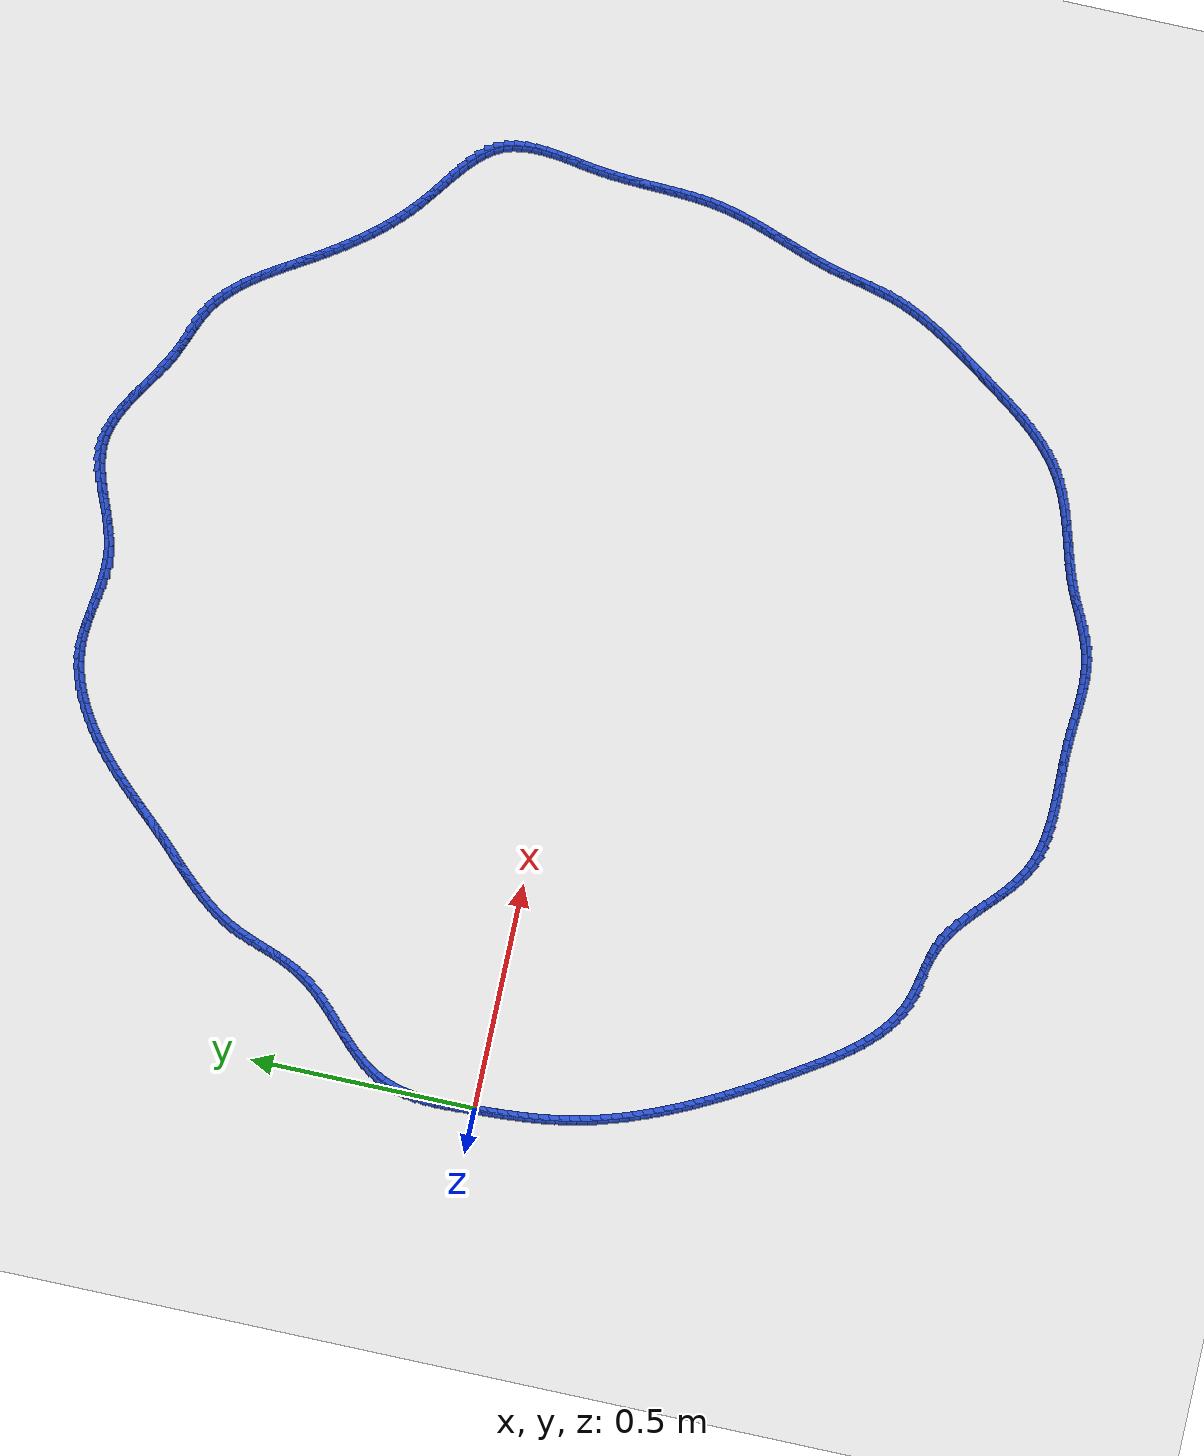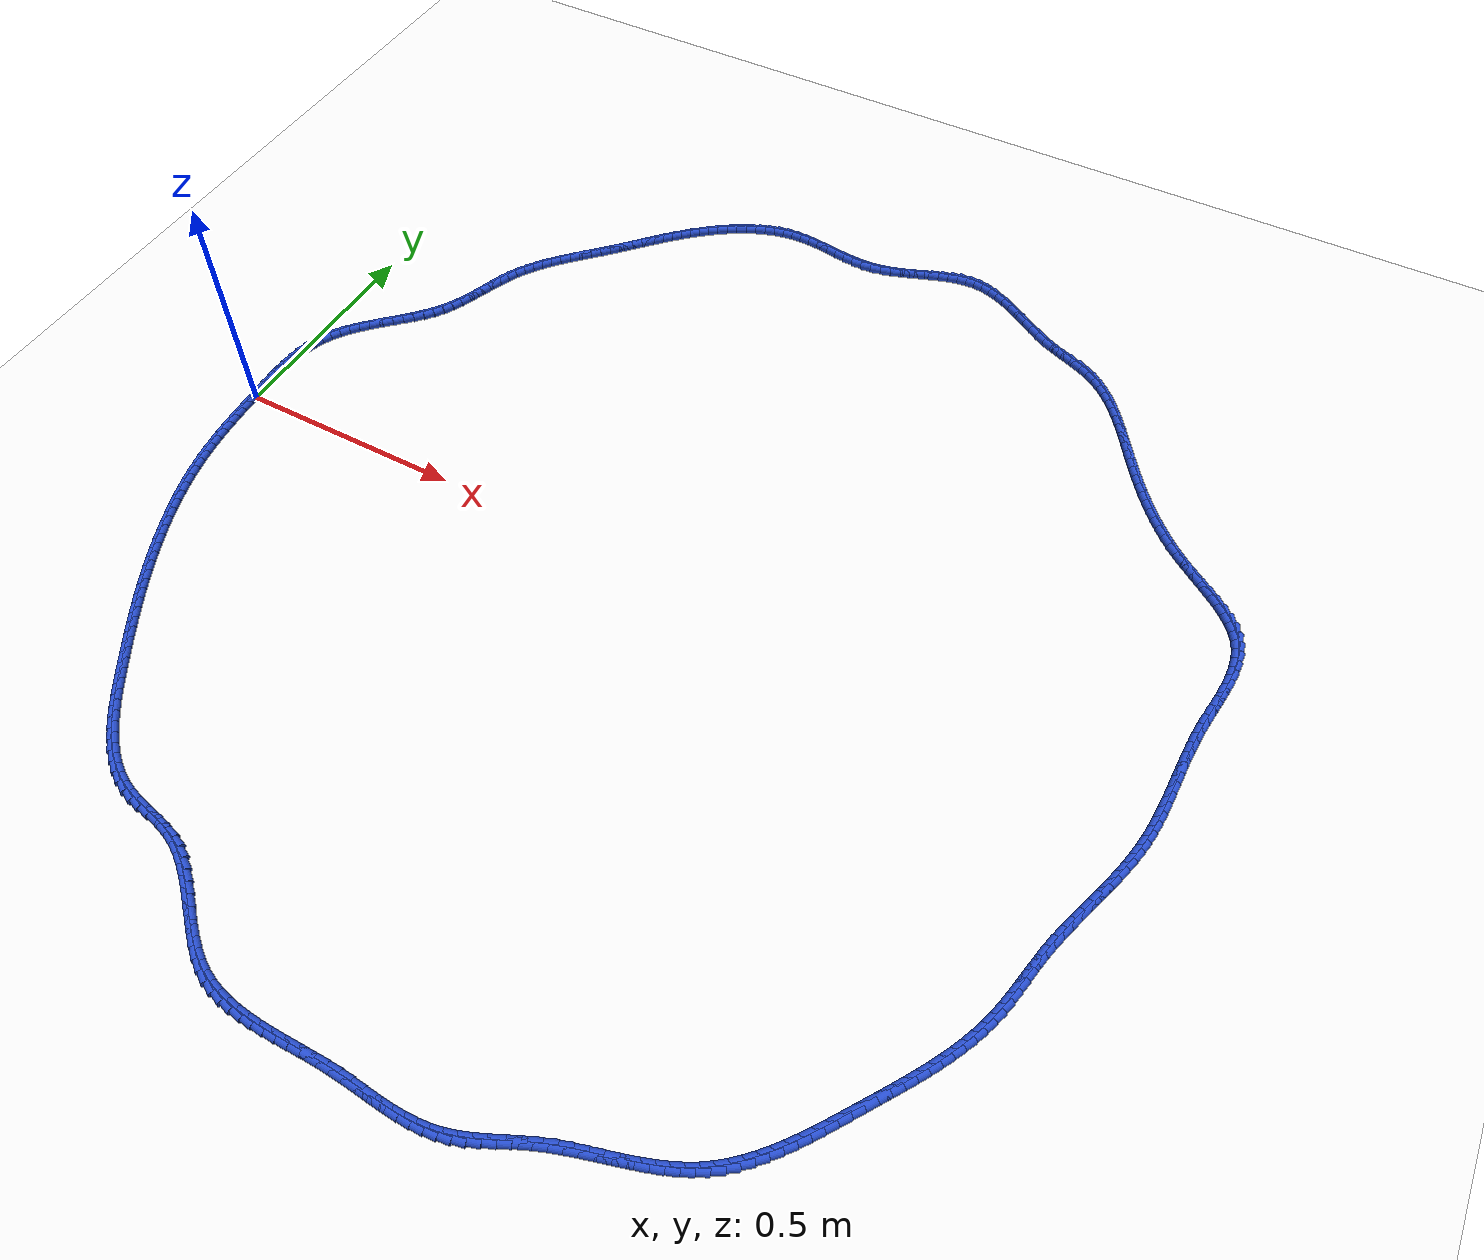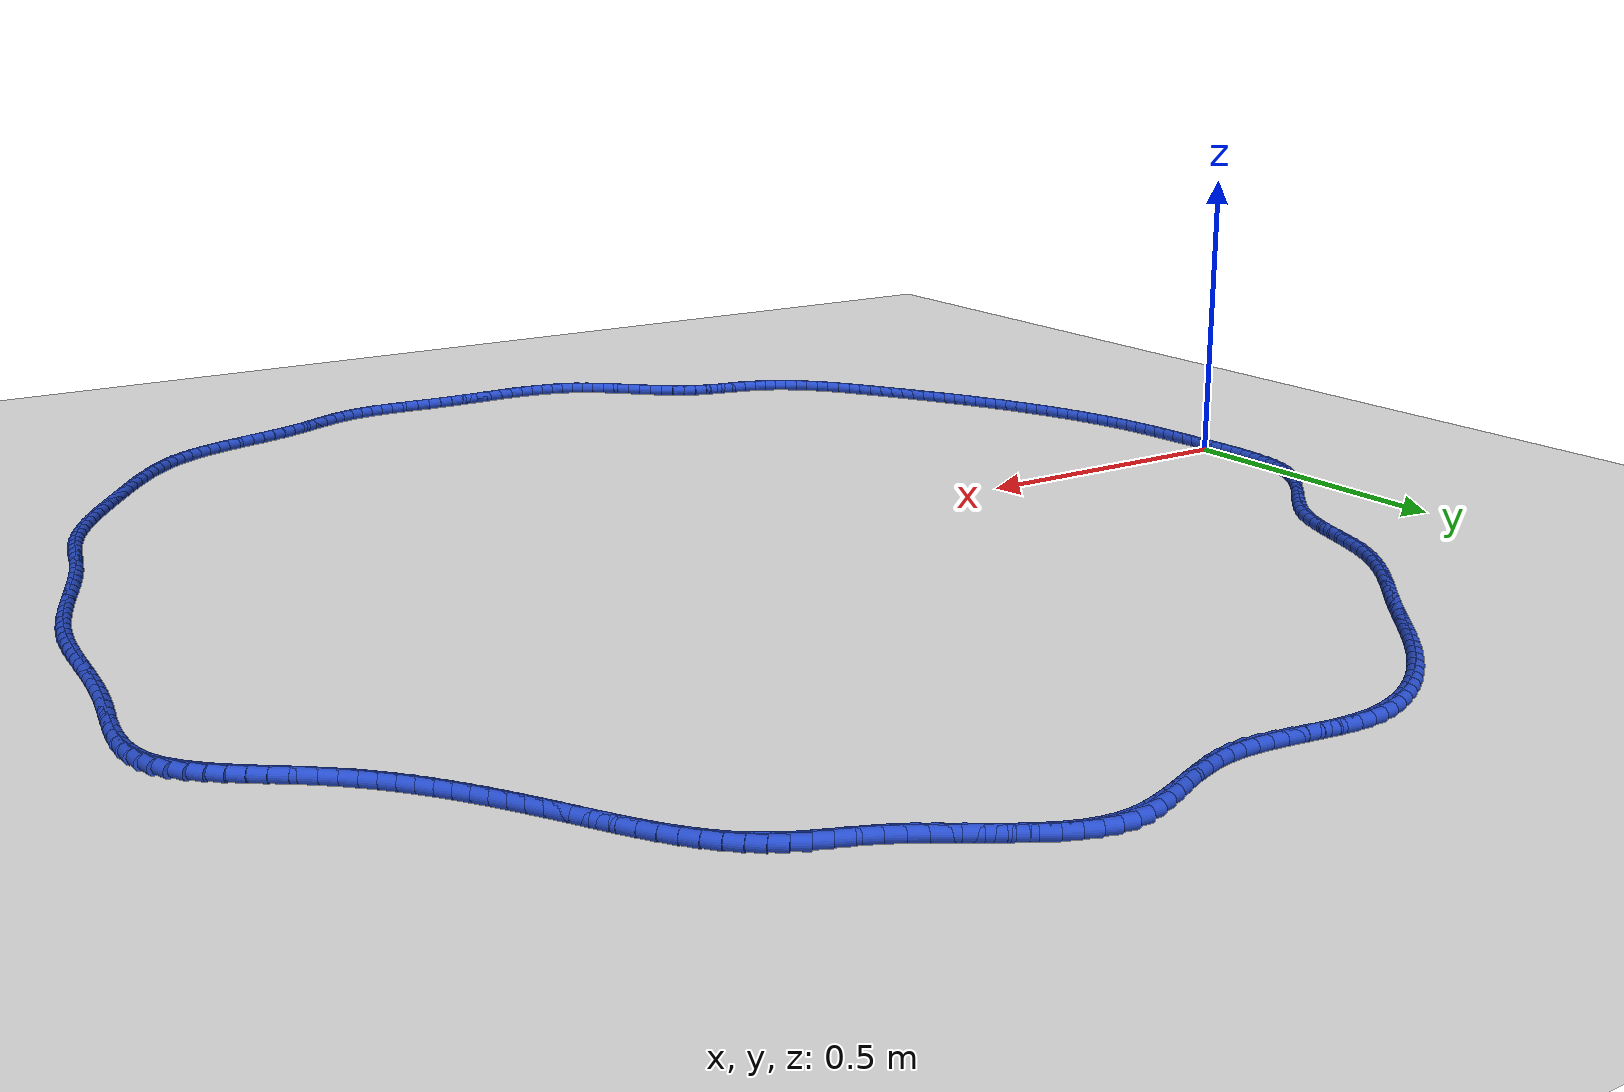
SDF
<sdf version="1.6">
 <world name="default">
  <light name="sun" type="directional">
   <pose>0 0 10 0 -0 0</pose>
   <diffuse>0.8 0.8 0.8 1</diffuse>
   <specular>0.2 0.2 0.2 1</specular>
   <attenuation>
    <range>1000</range>
    <constant>0.9</constant>
    <linear>0.01</linear>
    <quadratic>0.001</quadratic>
   </attenuation>
   <direction>-0.5 0.1 -0.9</direction>
  </light>
  <model name="ground_plane">
   <static>1</static>
   <link name="link">
    <collision name="collision">
     <geometry><plane><normal>0 0 1</normal><size>100 100</size></plane></geometry>
     <surface><friction><ode><mu>100</mu><mu2>50</mu2></ode></friction></surface>
    </collision>
    <visual name="visual">
     <cast_shadows>0</cast_shadows>
     <geometry><plane><normal>0 0 1</normal><size>100 100</size></plane></geometry>
     <material>
      <script><uri>file://media/materials/scripts/gazebo.material</uri><name>Gazebo/WhiteGlow</name></script>
     </material>
    </visual>
   </link>
  </model>
  <gravity>0 0 -9.8</gravity>
  <magnetic_field>6e-06 2.3e-05 -4.2e-05</magnetic_field>
  <atmosphere type="adiabatic"/>
  <physics name="default_physics" default="0" type="ode">
   <max_step_size>0.001</max_step_size>
   <real_time_factor>1</real_time_factor>
   <real_time_update_rate>1000</real_time_update_rate>
  </physics>
  <scene><ambient>0.4 0.4 0.4 1</ambient><background>0.7 0.7 0.7 1</background><shadows>1</shadows></scene>
  <spherical_coordinates>
   <surface_model>EARTH_WGS84</surface_model>
   <latitude_deg>0</latitude_deg>
   <longitude_deg>0</longitude_deg>
   <elevation>0</elevation>
   <heading_deg>0</heading_deg>
  </spherical_coordinates>
  <model name="line">
   <link name="link_0">
    <pose>-8.673617379884035e-19 6.938893903907228e-18 0.01 0 1.57 -1.5246301149782158</pose>
    <collision name="collision">
     <geometry><cylinder><radius>0.01</radius><length>0.08</length></cylinder></geometry>
    </collision>
    <visual name="visual">
     <material>
      <script><name>Gazebo/Blue</name><uri>file://media/materials/scripts/gazebo.material</uri></script>
     </material>
     <geometry><cylinder><radius>0.01</radius><length>0.08</length></cylinder></geometry>
    </visual>
   </link>
   <link name="link_1">
    <pose>-0.0011001443735072457 0.02381314456885705 0.01 0 1.57 -1.5374210759758733</pose>
    <collision name="collision">
     <geometry><cylinder><radius>0.01</radius><length>0.08</length></cylinder></geometry>
    </collision>
    <visual name="visual">
     <material>
      <script><name>Gazebo/Blue</name><uri>file://media/materials/scripts/gazebo.material</uri></script>
     </material>
     <geometry><cylinder><radius>0.01</radius><length>0.08</length></cylinder></geometry>
    </visual>
   </link>
   <link name="link_2">
    <pose>-0.00189906913369826 0.04774189643846767 0.01 0 1.57 -1.5593118271903437</pose>
    <collision name="collision">
     <geometry><cylinder><radius>0.01</radius><length>0.08</length></cylinder></geometry>
    </collision>
    <visual name="visual">
     <material>
      <script><name>Gazebo/Blue</name><uri>file://media/materials/scripts/gazebo.material</uri></script>
     </material>
     <geometry><cylinder><radius>0.01</radius><length>0.08</length></cylinder></geometry>
    </visual>
   </link>
   <link name="link_3">
    <pose>-0.002173610051218639 0.0716461897722483 0.01 0 1.57 1.5508742889381562</pose>
    <collision name="collision">
     <geometry><cylinder><radius>0.01</radius><length>0.08</length></cylinder></geometry>
    </collision>
    <visual name="visual">
     <material>
      <script><name>Gazebo/Blue</name><uri>file://media/materials/scripts/gazebo.material</uri></script>
     </material>
     <geometry><cylinder><radius>0.01</radius><length>0.08</length></cylinder></geometry>
    </visual>
   </link>
   <link name="link_4">
    <pose>-0.0017006028967139755 0.09538595873361543 0.01 0 1.57 1.509269284869773</pose>
    <collision name="collision">
     <geometry><cylinder><radius>0.01</radius><length>0.08</length></cylinder></geometry>
    </collision>
    <visual name="visual">
     <material>
      <script><name>Gazebo/Blue</name><uri>file://media/materials/scripts/gazebo.material</uri></script>
     </material>
     <geometry><cylinder><radius>0.01</radius><length>0.08</length></cylinder></geometry>
    </visual>
   </link>
   <link name="link_5">
    <pose>-0.0002568834408298651 0.11882113748598544 0.01 0 1.57 1.4565703640862406</pose>
    <collision name="collision">
     <geometry><cylinder><radius>0.01</radius><length>0.08</length></cylinder></geometry>
    </collision>
    <visual name="visual">
     <material>
      <script><name>Gazebo/Blue</name><uri>file://media/materials/scripts/gazebo.material</uri></script>
     </material>
     <geometry><cylinder><radius>0.01</radius><length>0.08</length></cylinder></geometry>
    </visual>
   </link>
   <link name="link_6">
    <pose>0.002380712545788097 0.14181166019277477 0.01 0 1.57 1.3917700840922864</pose>
    <collision name="collision">
     <geometry><cylinder><radius>0.01</radius><length>0.08</length></cylinder></geometry>
    </collision>
    <visual name="visual">
     <material>
      <script><name>Gazebo/Blue</name><uri>file://media/materials/scripts/gazebo.material</uri></script>
     </material>
     <geometry><cylinder><radius>0.01</radius><length>0.08</length></cylinder></geometry>
    </visual>
   </link>
   <link name="link_7">
    <pose>0.006435349292494319 0.16421746101739998 0.01 0 1.57 1.3139337070165626</pose>
    <collision name="collision">
     <geometry><cylinder><radius>0.01</radius><length>0.08</length></cylinder></geometry>
    </collision>
    <visual name="visual">
     <material>
      <script><name>Gazebo/Blue</name><uri>file://media/materials/scripts/gazebo.material</uri></script>
     </material>
     <geometry><cylinder><radius>0.01</radius><length>0.08</length></cylinder></geometry>
    </visual>
   </link>
   <link name="link_8">
    <pose>0.012130191028643203 0.18589847412327737 0.01 0 1.57 1.2225049243105828</pose>
    <collision name="collision">
     <geometry><cylinder><radius>0.01</radius><length>0.08</length></cylinder></geometry>
    </collision>
    <visual name="visual">
     <material>
      <script><name>Gazebo/Blue</name><uri>file://media/materials/scripts/gazebo.material</uri></script>
     </material>
     <geometry><cylinder><radius>0.01</radius><length>0.08</length></cylinder></geometry>
    </visual>
   </link>
   <link name="link_9">
    <pose>0.019688401983589152 0.20671463367382342 0.01 0 1.57 1.1187030326941942</pose>
    <collision name="collision">
     <geometry><cylinder><radius>0.01</radius><length>0.08</length></cylinder></geometry>
    </collision>
    <visual name="visual">
     <material>
      <script><name>Gazebo/Blue</name><uri>file://media/materials/scripts/gazebo.material</uri></script>
     </material>
     <geometry><cylinder><radius>0.01</radius><length>0.08</length></cylinder></geometry>
    </visual>
   </link>
   <link name="link_10">
    <pose>0.029314615154590298 0.22653636264551447 0.01 0 1.57 1.0190187588300657</pose>
    <collision name="collision">
     <geometry><cylinder><radius>0.01</radius><length>0.08</length></cylinder></geometry>
    </collision>
    <visual name="visual">
     <material>
      <script><name>Gazebo/Blue</name><uri>file://media/materials/scripts/gazebo.material</uri></script>
     </material>
     <geometry><cylinder><radius>0.01</radius><length>0.08</length></cylinder></geometry>
    </visual>
   </link>
   <link name="link_11">
    <pose>0.04092467999508773 0.24539753761521904 0.01 0 1.57 0.9368000062690974</pose>
    <collision name="collision">
     <geometry><cylinder><radius>0.01</radius><length>0.08</length></cylinder></geometry>
    </collision>
    <visual name="visual">
     <material>
      <script><name>Gazebo/Blue</name><uri>file://media/materials/scripts/gazebo.material</uri></script>
     </material>
     <geometry><cylinder><radius>0.01</radius><length>0.08</length></cylinder></geometry>
    </visual>
   </link>
   <link name="link_12">
    <pose>0.05420610657575608 0.2634612769224467 0.01 0 1.57 0.8724598786086498</pose>
    <collision name="collision">
     <geometry><cylinder><radius>0.01</radius><length>0.08</length></cylinder></geometry>
    </collision>
    <visual name="visual">
     <material>
      <script><name>Gazebo/Blue</name><uri>file://media/materials/scripts/gazebo.material</uri></script>
     </material>
     <geometry><cylinder><radius>0.01</radius><length>0.08</length></cylinder></geometry>
    </visual>
   </link>
   <link name="link_13">
    <pose>0.06884017195413805 0.2808942268377802 0.01 0 1.57 0.8252347236240744</pose>
    <collision name="collision">
     <geometry><cylinder><radius>0.01</radius><length>0.08</length></cylinder></geometry>
    </collision>
    <visual name="visual">
     <material>
      <script><name>Gazebo/Blue</name><uri>file://media/materials/scripts/gazebo.material</uri></script>
     </material>
     <geometry><cylinder><radius>0.01</radius><length>0.08</length></cylinder></geometry>
    </visual>
   </link>
   <link name="link_14">
    <pose>0.08450815318777634 0.29786303363180217 0.01 0 1.57 0.7941149383532964</pose>
    <collision name="collision">
     <geometry><cylinder><radius>0.01</radius><length>0.08</length></cylinder></geometry>
    </collision>
    <visual name="visual">
     <material>
      <script><name>Gazebo/Blue</name><uri>file://media/materials/scripts/gazebo.material</uri></script>
     </material>
     <geometry><cylinder><radius>0.01</radius><length>0.08</length></cylinder></geometry>
    </visual>
   </link>
   <link name="link_15">
    <pose>0.10089132733421366 0.3145343435750956 0.01 0 1.57 0.7782198950117848</pose>
    <collision name="collision">
     <geometry><cylinder><radius>0.01</radius><length>0.08</length></cylinder></geometry>
    </collision>
    <visual name="visual">
     <material>
      <script><name>Gazebo/Blue</name><uri>file://media/materials/scripts/gazebo.material</uri></script>
     </material>
     <geometry><cylinder><radius>0.01</radius><length>0.08</length></cylinder></geometry>
    </visual>
   </link>
   <link name="link_16">
    <pose>0.11767097145099276 0.33107480293824315 0.01 0 1.57 0.7769895841014264</pose>
    <collision name="collision">
     <geometry><cylinder><radius>0.01</radius><length>0.08</length></cylinder></geometry>
    </collision>
    <visual name="visual">
     <material>
      <script><name>Gazebo/Blue</name><uri>file://media/materials/scripts/gazebo.material</uri></script>
     </material>
     <geometry><cylinder><radius>0.01</radius><length>0.08</length></cylinder></geometry>
    </visual>
   </link>
   <link name="link_17">
    <pose>0.13452836259565634 0.3476510579918277 0.01 0 1.57 0.790257572341971</pose>
    <collision name="collision">
     <geometry><cylinder><radius>0.01</radius><length>0.08</length></cylinder></geometry>
    </collision>
    <visual name="visual">
     <material>
      <script><name>Gazebo/Blue</name><uri>file://media/materials/scripts/gazebo.material</uri></script>
     </material>
     <geometry><cylinder><radius>0.01</radius><length>0.08</length></cylinder></geometry>
    </visual>
   </link>
   <link name="link_18">
    <pose>0.1511447778257471 0.3644297550064319 0.01 0 1.57 0.8182454097606433</pose>
    <collision name="collision">
     <geometry><cylinder><radius>0.01</radius><length>0.08</length></cylinder></geometry>
    </collision>
    <visual name="visual">
     <material>
      <script><name>Gazebo/Blue</name><uri>file://media/materials/scripts/gazebo.material</uri></script>
     </material>
     <geometry><cylinder><radius>0.01</radius><length>0.08</length></cylinder></geometry>
    </visual>
   </link>
   <link name="link_19">
    <pose>0.16720149419880778 0.3815775402526387 0.01 0 1.57 0.8614861333797638</pose>
    <collision name="collision">
     <geometry><cylinder><radius>0.01</radius><length>0.08</length></cylinder></geometry>
    </collision>
    <visual name="visual">
     <material>
      <script><name>Gazebo/Blue</name><uri>file://media/materials/scripts/gazebo.material</uri></script>
     </material>
     <geometry><cylinder><radius>0.01</radius><length>0.08</length></cylinder></geometry>
    </visual>
   </link>
   <link name="link_20">
    <pose>0.18237978877238106 0.39926106000103073 0.01 0 1.57 0.9206547636802748</pose>
    <collision name="collision">
     <geometry><cylinder><radius>0.01</radius><length>0.08</length></cylinder></geometry>
    </collision>
    <visual name="visual">
     <material>
      <script><name>Gazebo/Blue</name><uri>file://media/materials/scripts/gazebo.material</uri></script>
     </material>
     <geometry><cylinder><radius>0.01</radius><length>0.08</length></cylinder></geometry>
    </visual>
   </link>
   <link name="link_21">
    <pose>0.19636093860400966 0.4176469605221909 0.01 0 1.57 0.9961611812305781</pose>
    <collision name="collision">
     <geometry><cylinder><radius>0.01</radius><length>0.08</length></cylinder></geometry>
    </collision>
    <visual name="visual">
     <material>
      <script><name>Gazebo/Blue</name><uri>file://media/materials/scripts/gazebo.material</uri></script>
     </material>
     <geometry><cylinder><radius>0.01</radius><length>0.08</length></cylinder></geometry>
    </visual>
   </link>
   <link name="link_22">
    <pose>0.20882829171628223 0.4369007410874593 0.01 0 1.57 1.076708419460473</pose>
    <collision name="collision">
     <geometry><cylinder><radius>0.01</radius><length>0.08</length></cylinder></geometry>
    </collision>
    <visual name="visual">
     <material>
      <script><name>Gazebo/Blue</name><uri>file://media/materials/scripts/gazebo.material</uri></script>
     </material>
     <geometry><cylinder><radius>0.01</radius><length>0.08</length></cylinder></geometry>
    </visual>
   </link>
   <link name="link_23">
    <pose>0.21968916532211782 0.45706385614562334 0.01 0 1.57 1.1405268804972584</pose>
    <collision name="collision">
     <geometry><cylinder><radius>0.01</radius><length>0.08</length></cylinder></geometry>
    </collision>
    <visual name="visual">
     <material>
      <script><name>Gazebo/Blue</name><uri>file://media/materials/scripts/gazebo.material</uri></script>
     </material>
     <geometry><cylinder><radius>0.01</radius><length>0.08</length></cylinder></geometry>
    </visual>
   </link>
   <link name="link_24">
    <pose>0.2292722296930821 0.4779443947200074 0.01 0 1.57 1.1851242442502838</pose>
    <collision name="collision">
     <geometry><cylinder><radius>0.01</radius><length>0.08</length></cylinder></geometry>
    </collision>
    <visual name="visual">
     <material>
      <script><name>Gazebo/Blue</name><uri>file://media/materials/scripts/gazebo.material</uri></script>
     </material>
     <geometry><cylinder><radius>0.01</radius><length>0.08</length></cylinder></geometry>
    </visual>
   </link>
   <link name="link_25">
    <pose>0.23795271657178255 0.499324657869954 0.01 0 1.57 1.2108208360700574</pose>
    <collision name="collision">
     <geometry><cylinder><radius>0.01</radius><length>0.08</length></cylinder></geometry>
    </collision>
    <visual name="visual">
     <material>
      <script><name>Gazebo/Blue</name><uri>file://media/materials/scripts/gazebo.material</uri></script>
     </material>
     <geometry><cylinder><radius>0.01</radius><length>0.08</length></cylinder></geometry>
    </visual>
   </link>
   <link name="link_26">
    <pose>0.24610585770082669 0.520986946654806 0.01 0 1.57 1.2179484116636439</pose>
    <collision name="collision">
     <geometry><cylinder><radius>0.01</radius><length>0.08</length></cylinder></geometry>
    </collision>
    <visual name="visual">
     <material>
      <script><name>Gazebo/Blue</name><uri>file://media/materials/scripts/gazebo.material</uri></script>
     </material>
     <geometry><cylinder><radius>0.01</radius><length>0.08</length></cylinder></geometry>
    </visual>
   </link>
   <link name="link_27">
    <pose>0.2541068848228222 0.5427135621339064 0.01 0 1.57 1.2065839684980628</pose>
    <collision name="collision">
     <geometry><cylinder><radius>0.01</radius><length>0.08</length></cylinder></geometry>
    </collision>
    <visual name="visual">
     <material>
      <script><name>Gazebo/Blue</name><uri>file://media/materials/scripts/gazebo.material</uri></script>
     </material>
     <geometry><cylinder><radius>0.01</radius><length>0.08</length></cylinder></geometry>
    </visual>
   </link>
   <link name="link_28">
    <pose>0.26233102968037636 0.5642868053665977 0.01 0 1.57 1.176477267388566</pose>
    <collision name="collision">
     <geometry><cylinder><radius>0.01</radius><length>0.08</length></cylinder></geometry>
    </collision>
    <visual name="visual">
     <material>
      <script><name>Gazebo/Blue</name><uri>file://media/materials/scripts/gazebo.material</uri></script>
     </material>
     <geometry><cylinder><radius>0.01</radius><length>0.08</length></cylinder></geometry>
    </visual>
   </link>
   <link name="link_29">
    <pose>0.2711535240160968 0.5854889774122227 0.01 0 1.57 1.127161591847886</pose>
    <collision name="collision">
     <geometry><cylinder><radius>0.01</radius><length>0.08</length></cylinder></geometry>
    </collision>
    <visual name="visual">
     <material>
      <script><name>Gazebo/Blue</name><uri>file://media/materials/scripts/gazebo.material</uri></script>
     </material>
     <geometry><cylinder><radius>0.01</radius><length>0.08</length></cylinder></geometry>
    </visual>
   </link>
   <link name="link_30">
    <pose>0.2809495995725911 0.6061023793301241 0.01 0 1.57 1.061831958757235</pose>
    <collision name="collision">
     <geometry><cylinder><radius>0.01</radius><length>0.08</length></cylinder></geometry>
    </collision>
    <visual name="visual">
     <material>
      <script><name>Gazebo/Blue</name><uri>file://media/materials/scripts/gazebo.material</uri></script>
     </material>
     <geometry><cylinder><radius>0.01</radius><length>0.08</length></cylinder></geometry>
    </visual>
   </link>
   <link name="link_31">
    <pose>0.29202459085986376 0.6259500396720835 0.01 0 1.57 0.9988459904425757</pose>
    <collision name="collision">
     <geometry><cylinder><radius>0.01</radius><length>0.08</length></cylinder></geometry>
    </collision>
    <visual name="visual">
     <material>
      <script><name>Gazebo/Blue</name><uri>file://media/materials/scripts/gazebo.material</uri></script>
     </material>
     <geometry><cylinder><radius>0.01</radius><length>0.08</length></cylinder></geometry>
    </visual>
   </link>
   <link name="link_32">
    <pose>0.3043277225309878 0.6450624839245311 0.01 0 1.57 0.9444124546212812</pose>
    <collision name="collision">
     <geometry><cylinder><radius>0.01</radius><length>0.08</length></cylinder></geometry>
    </collision>
    <visual name="visual">
     <material>
      <script><name>Gazebo/Blue</name><uri>file://media/materials/scripts/gazebo.material</uri></script>
     </material>
     <geometry><cylinder><radius>0.01</radius><length>0.08</length></cylinder></geometry>
    </visual>
   </link>
   <link name="link_33">
    <pose>0.3176950976063015 0.6635361509193938 0.01 0 1.57 0.8986932509911858</pose>
    <collision name="collision">
     <geometry><cylinder><radius>0.01</radius><length>0.08</length></cylinder></geometry>
    </collision>
    <visual name="visual">
     <material>
      <script><name>Gazebo/Blue</name><uri>file://media/materials/scripts/gazebo.material</uri></script>
     </material>
     <geometry><cylinder><radius>0.01</radius><length>0.08</length></cylinder></geometry>
    </visual>
   </link>
   <link name="link_34">
    <pose>0.33196277250657735 0.6814675066410825 0.01 0 1.57 0.8616279497944331</pose>
    <collision name="collision">
     <geometry><cylinder><radius>0.01</radius><length>0.08</length></cylinder></geometry>
    </collision>
    <visual name="visual">
     <material>
      <script><name>Gazebo/Blue</name><uri>file://media/materials/scripts/gazebo.material</uri></script>
     </material>
     <geometry><cylinder><radius>0.01</radius><length>0.08</length></cylinder></geometry>
    </visual>
   </link>
   <link name="link_35">
    <pose>0.34696680365258775 0.6989530170740083 0.01 0 1.57 0.8330406091377653</pose>
    <collision name="collision">
     <geometry><cylinder><radius>0.01</radius><length>0.08</length></cylinder></geometry>
    </collision>
    <visual name="visual">
     <material>
      <script><name>Gazebo/Blue</name><uri>file://media/materials/scripts/gazebo.material</uri></script>
     </material>
     <geometry><cylinder><radius>0.01</radius><length>0.08</length></cylinder></geometry>
    </visual>
   </link>
   <link name="link_36">
    <pose>0.362543247465105 0.716089148202582 0.01 0 1.57 0.8127219364148226</pose>
    <collision name="collision">
     <geometry><cylinder><radius>0.01</radius><length>0.08</length></cylinder></geometry>
    </collision>
    <visual name="visual">
     <material>
      <script><name>Gazebo/Blue</name><uri>file://media/materials/scripts/gazebo.material</uri></script>
     </material>
     <geometry><cylinder><radius>0.01</radius><length>0.08</length></cylinder></geometry>
    </visual>
   </link>
   <link name="link_37">
    <pose>0.37852816036490117 0.7329723660112146 0.01 0 1.57 0.8004877120736859</pose>
    <collision name="collision">
     <geometry><cylinder><radius>0.01</radius><length>0.08</length></cylinder></geometry>
    </collision>
    <visual name="visual">
     <material>
      <script><name>Gazebo/Blue</name><uri>file://media/materials/scripts/gazebo.material</uri></script>
     </material>
     <geometry><cylinder><radius>0.01</radius><length>0.08</length></cylinder></geometry>
    </visual>
   </link>
   <link name="link_38">
    <pose>0.39475759877274863 0.749699136484317 0.01 0 1.57 0.7962165194694196</pose>
    <collision name="collision">
     <geometry><cylinder><radius>0.01</radius><length>0.08</length></cylinder></geometry>
    </collision>
    <visual name="visual">
     <material>
      <script><name>Gazebo/Blue</name><uri>file://media/materials/scripts/gazebo.material</uri></script>
     </material>
     <geometry><cylinder><radius>0.01</radius><length>0.08</length></cylinder></geometry>
    </visual>
   </link>
   <link name="link_39">
    <pose>0.4110676191094199 0.7663659256063005 0.01 0 1.57 0.7998707649653242</pose>
    <collision name="collision">
     <geometry><cylinder><radius>0.01</radius><length>0.08</length></cylinder></geometry>
    </collision>
    <visual name="visual">
     <material>
      <script><name>Gazebo/Blue</name><uri>file://media/materials/scripts/gazebo.material</uri></script>
     </material>
     <geometry><cylinder><radius>0.01</radius><length>0.08</length></cylinder></geometry>
    </visual>
   </link>
   <link name="link_40">
    <pose>0.42729427779568707 0.7830691993615756 0.01 0 1.57 0.8111536940769282</pose>
    <collision name="collision">
     <geometry><cylinder><radius>0.01</radius><length>0.08</length></cylinder></geometry>
    </collision>
    <visual name="visual">
     <material>
      <script><name>Gazebo/Blue</name><uri>file://media/materials/scripts/gazebo.material</uri></script>
     </material>
     <geometry><cylinder><radius>0.01</radius><length>0.08</length></cylinder></geometry>
    </visual>
   </link>
   <link name="link_41">
    <pose>0.4432805434828458 0.7999008960314637 0.01 0 1.57 0.8234440319376947</pose>
    <collision name="collision">
     <geometry><cylinder><radius>0.01</radius><length>0.08</length></cylinder></geometry>
    </collision>
    <visual name="visual">
     <material>
      <script><name>Gazebo/Blue</name><uri>file://media/materials/scripts/gazebo.material</uri></script>
     </material>
     <geometry><cylinder><radius>0.01</radius><length>0.08</length></cylinder></geometry>
    </visual>
   </link>
   <link name="link_42">
    <pose>0.4590017257110101 0.8168662669372408 0.01 0 1.57 0.8306716103659707</pose>
    <collision name="collision">
     <geometry><cylinder><radius>0.01</radius><length>0.08</length></cylinder></geometry>
    </collision>
    <visual name="visual">
     <material>
      <script><name>Gazebo/Blue</name><uri>file://media/materials/scripts/gazebo.material</uri></script>
     </material>
     <geometry><cylinder><radius>0.01</radius><length>0.08</length></cylinder></geometry>
    </visual>
   </link>
   <link name="link_43">
    <pose>0.4745521754985508 0.8338925879236561 0.01 0 1.57 0.8325608416837419</pose>
    <collision name="collision">
     <geometry><cylinder><radius>0.01</radius><length>0.08</length></cylinder></geometry>
    </collision>
    <visual name="visual">
     <material>
      <script><name>Gazebo/Blue</name><uri>file://media/materials/scripts/gazebo.material</uri></script>
     </material>
     <geometry><cylinder><radius>0.01</radius><length>0.08</length></cylinder></geometry>
    </visual>
   </link>
   <link name="link_44">
    <pose>0.49003048685603245 0.8509043555576565 0.01 0 1.57 0.8290675096566906</pose>
    <collision name="collision">
     <geometry><cylinder><radius>0.01</radius><length>0.08</length></cylinder></geometry>
    </collision>
    <visual name="visual">
     <material>
      <script><name>Gazebo/Blue</name><uri>file://media/materials/scripts/gazebo.material</uri></script>
     </material>
     <geometry><cylinder><radius>0.01</radius><length>0.08</length></cylinder></geometry>
    </visual>
   </link>
   <link name="link_45">
    <pose>0.5055352537940191 0.8678260664061891 0.01 0 1.57 0.8201626127285712</pose>
    <collision name="collision">
     <geometry><cylinder><radius>0.01</radius><length>0.08</length></cylinder></geometry>
    </collision>
    <visual name="visual">
     <material>
      <script><name>Gazebo/Blue</name><uri>file://media/materials/scripts/gazebo.material</uri></script>
     </material>
     <geometry><cylinder><radius>0.01</radius><length>0.08</length></cylinder></geometry>
    </visual>
   </link>
   <link name="link_46">
    <pose>0.5211650703230748 0.8845822170362005 0.01 0 1.57 0.8058357420020107</pose>
    <collision name="collision">
     <geometry><cylinder><radius>0.01</radius><length>0.08</length></cylinder></geometry>
    </collision>
    <visual name="visual">
     <material>
      <script><name>Gazebo/Blue</name><uri>file://media/materials/scripts/gazebo.material</uri></script>
     </material>
     <geometry><cylinder><radius>0.01</radius><length>0.08</length></cylinder></geometry>
    </visual>
   </link>
   <link name="link_47">
    <pose>0.537018530453764 0.9010973040146381 0.01 0 1.57 0.786103111618877</pose>
    <collision name="collision">
     <geometry><cylinder><radius>0.01</radius><length>0.08</length></cylinder></geometry>
    </collision>
    <visual name="visual">
     <material>
      <script><name>Gazebo/Blue</name><uri>file://media/materials/scripts/gazebo.material</uri></script>
     </material>
     <geometry><cylinder><radius>0.01</radius><length>0.08</length></cylinder></geometry>
    </visual>
   </link>
   <link name="link_48">
    <pose>0.5531942281966508 0.9172958239084484 0.01 0 1.57 0.7610200506081204</pose>
    <collision name="collision">
     <geometry><cylinder><radius>0.01</radius><length>0.08</length></cylinder></geometry>
    </collision>
    <visual name="visual">
     <material>
      <script><name>Gazebo/Blue</name><uri>file://media/materials/scripts/gazebo.material</uri></script>
     </material>
     <geometry><cylinder><radius>0.01</radius><length>0.08</length></cylinder></geometry>
    </visual>
   </link>
   <link name="link_49">
    <pose>0.569790757562299 0.9331022732845782 0.01 0 1.57 0.730697314627442</pose>
    <collision name="collision">
     <geometry><cylinder><radius>0.01</radius><length>0.08</length></cylinder></geometry>
    </collision>
    <visual name="visual">
     <material>
      <script><name>Gazebo/Blue</name><uri>file://media/materials/scripts/gazebo.material</uri></script>
     </material>
     <geometry><cylinder><radius>0.01</radius><length>0.08</length></cylinder></geometry>
    </visual>
   </link>
   <link name="link_50">
    <pose>0.5869067125612736 0.9484411487099748 0.01 0 1.57 0.6953199003946172</pose>
    <collision name="collision">
     <geometry><cylinder><radius>0.01</radius><length>0.08</length></cylinder></geometry>
    </collision>
    <visual name="visual">
     <material>
      <script><name>Gazebo/Blue</name><uri>file://media/materials/scripts/gazebo.material</uri></script>
     </material>
     <geometry><cylinder><radius>0.01</radius><length>0.08</length></cylinder></geometry>
    </visual>
   </link>
   <link name="link_51">
    <pose>0.6046406872041376 0.9632369467515843 0.01 0 1.57 0.6551661998020621</pose>
    <collision name="collision">
     <geometry><cylinder><radius>0.01</radius><length>0.08</length></cylinder></geometry>
    </collision>
    <visual name="visual">
     <material>
      <script><name>Gazebo/Blue</name><uri>file://media/materials/scripts/gazebo.material</uri></script>
     </material>
     <geometry><cylinder><radius>0.01</radius><length>0.08</length></cylinder></geometry>
    </visual>
   </link>
   <link name="link_52">
    <pose>0.623091268279836 0.977414159512706 0.01 0 1.57 0.6107275105724828</pose>
    <collision name="collision">
     <geometry><cylinder><radius>0.01</radius><length>0.08</length></cylinder></geometry>
    </collision>
    <visual name="visual">
     <material>
      <script><name>Gazebo/Blue</name><uri>file://media/materials/scripts/gazebo.material</uri></script>
     </material>
     <geometry><cylinder><radius>0.01</radius><length>0.08</length></cylinder></geometry>
    </visual>
   </link>
   <link name="link_53">
    <pose>0.6423208209695195 0.9908748906968274 0.01 0 1.57 0.5622989030775445</pose>
    <collision name="collision">
     <geometry><cylinder><radius>0.01</radius><length>0.08</length></cylinder></geometry>
    </collision>
    <visual name="visual">
     <material>
      <script><name>Gazebo/Blue</name><uri>file://media/materials/scripts/gazebo.material</uri></script>
     </material>
     <geometry><cylinder><radius>0.01</radius><length>0.08</length></cylinder></geometry>
    </visual>
   </link>
   <link name="link_54">
    <pose>0.6622713364170622 1.003446841399776 0.01 0 1.57 0.5092257444733604</pose>
    <collision name="collision">
     <geometry><cylinder><radius>0.01</radius><length>0.08</length></cylinder></geometry>
    </collision>
    <visual name="visual">
     <material>
      <script><name>Gazebo/Blue</name><uri>file://media/materials/scripts/gazebo.material</uri></script>
     </material>
     <geometry><cylinder><radius>0.01</radius><length>0.08</length></cylinder></geometry>
    </visual>
   </link>
   <link name="link_55">
    <pose>0.6828598322182717 1.0149422766886425 0.01 0 1.57 0.4506790373590013</pose>
    <collision name="collision">
     <geometry><cylinder><radius>0.01</radius><length>0.08</length></cylinder></geometry>
    </collision>
    <visual name="visual">
     <material>
      <script><name>Gazebo/Blue</name><uri>file://media/materials/scripts/gazebo.material</uri></script>
     </material>
     <geometry><cylinder><radius>0.01</radius><length>0.08</length></cylinder></geometry>
    </visual>
   </link>
   <link name="link_56">
    <pose>0.7040033259689559 1.025173461630518 0.01 0 1.57 0.3857992374001578</pose>
    <collision name="collision">
     <geometry><cylinder><radius>0.01</radius><length>0.08</length></cylinder></geometry>
    </collision>
    <visual name="visual">
     <material>
      <script><name>Gazebo/Blue</name><uri>file://media/materials/scripts/gazebo.material</uri></script>
     </material>
     <geometry><cylinder><radius>0.01</radius><length>0.08</length></cylinder></geometry>
    </visual>
   </link>
   <link name="link_57">
    <pose>0.7256188352649215 1.0339526612924919 0.01 0 1.57 0.31373870671372317</pose>
    <collision name="collision">
     <geometry><cylinder><radius>0.01</radius><length>0.08</length></cylinder></geometry>
    </collision>
    <visual name="visual">
     <material>
      <script><name>Gazebo/Blue</name><uri>file://media/materials/scripts/gazebo.material</uri></script>
     </material>
     <geometry><cylinder><radius>0.01</radius><length>0.08</length></cylinder></geometry>
    </visual>
   </link>
   <link name="link_58">
    <pose>0.747623377701977 1.0410921407416551 0.01 0 1.57 0.23374226082552402</pose>
    <collision name="collision">
     <geometry><cylinder><radius>0.01</radius><length>0.08</length></cylinder></geometry>
    </collision>
    <visual name="visual">
     <material>
      <script><name>Gazebo/Blue</name><uri>file://media/materials/scripts/gazebo.material</uri></script>
     </material>
     <geometry><cylinder><radius>0.01</radius><length>0.08</length></cylinder></geometry>
    </visual>
   </link>
   <link name="link_59">
    <pose>0.769933970875929 1.0464041650450986 0.01 0 1.57 0.1452763483159616</pose>
    <collision name="collision">
     <geometry><cylinder><radius>0.01</radius><length>0.08</length></cylinder></geometry>
    </collision>
    <visual name="visual">
     <material>
      <script><name>Gazebo/Blue</name><uri>file://media/materials/scripts/gazebo.material</uri></script>
     </material>
     <geometry><cylinder><radius>0.01</radius><length>0.08</length></cylinder></geometry>
    </visual>
   </link>
   <link name="link_60">
    <pose>0.7924676323825858 1.0497009992699118 0.01 0 1.57 0.05052441961582209</pose>
    <collision name="collision">
     <geometry><cylinder><radius>0.01</radius><length>0.08</length></cylinder></geometry>
    </collision>
    <visual name="visual">
     <material>
      <script><name>Gazebo/Blue</name><uri>file://media/materials/scripts/gazebo.material</uri></script>
     </material>
     <geometry><cylinder><radius>0.01</radius><length>0.08</length></cylinder></geometry>
    </visual>
   </link>
   <link name="link_61">
    <pose>0.8151463044707263 1.050847802001864 0.01 0 1.57 -0.03127269319740061</pose>
    <collision name="collision">
     <geometry><cylinder><radius>0.01</radius><length>0.08</length></cylinder></geometry>
    </collision>
    <visual name="visual">
     <material>
      <script><name>Gazebo/Blue</name><uri>file://media/materials/scripts/gazebo.material</uri></script>
     </material>
     <geometry><cylinder><radius>0.01</radius><length>0.08</length></cylinder></geometry>
    </visual>
   </link>
   <link name="link_62">
    <pose>0.8379315253385867 1.0501350144007526 0.01 0 1.57 -0.09055951067852805</pose>
    <collision name="collision">
     <geometry><cylinder><radius>0.01</radius><length>0.08</length></cylinder></geometry>
    </collision>
    <visual name="visual">
     <material>
      <script><name>Gazebo/Blue</name><uri>file://media/materials/scripts/gazebo.material</uri></script>
     </material>
     <geometry><cylinder><radius>0.01</radius><length>0.08</length></cylinder></geometry>
    </visual>
   </link>
   <link name="link_63">
    <pose>0.8608039144542238 1.0480580211030643 0.01 0 1.57 -0.12765680810451685</pose>
    <collision name="collision">
     <geometry><cylinder><radius>0.01</radius><length>0.08</length></cylinder></geometry>
    </collision>
    <visual name="visual">
     <material>
      <script><name>Gazebo/Blue</name><uri>file://media/materials/scripts/gazebo.material</uri></script>
     </material>
     <geometry><cylinder><radius>0.01</radius><length>0.08</length></cylinder></geometry>
    </visual>
   </link>
   <link name="link_64">
    <pose>0.8837442138849907 1.0451135235301154 0.01 0 1.57 -0.1432253166122556</pose>
    <collision name="collision">
     <geometry><cylinder><radius>0.01</radius><length>0.08</length></cylinder></geometry>
    </collision>
    <visual name="visual">
     <material>
      <script><name>Gazebo/Blue</name><uri>file://media/materials/scripts/gazebo.material</uri></script>
     </material>
     <geometry><cylinder><radius>0.01</radius><length>0.08</length></cylinder></geometry>
    </visual>
   </link>
   <link name="link_65">
    <pose>0.9067331656982431 1.0417982231032235 0.01 0 1.57 -0.13768248358546092</pose>
    <collision name="collision">
     <geometry><cylinder><radius>0.01</radius><length>0.08</length></cylinder></geometry>
    </collision>
    <visual name="visual">
     <material>
      <script><name>Gazebo/Blue</name><uri>file://media/materials/scripts/gazebo.material</uri></script>
     </material>
     <geometry><cylinder><radius>0.01</radius><length>0.08</length></cylinder></geometry>
    </visual>
   </link>
   <link name="link_66">
    <pose>0.9297515119613357 1.0386088212437046 0.01 0 1.57 -0.11100386574259463</pose>
    <collision name="collision">
     <geometry><cylinder><radius>0.01</radius><length>0.08</length></cylinder></geometry>
    </collision>
    <visual name="visual">
     <material>
      <script><name>Gazebo/Blue</name><uri>file://media/materials/scripts/gazebo.material</uri></script>
     </material>
     <geometry><cylinder><radius>0.01</radius><length>0.08</length></cylinder></geometry>
    </visual>
   </link>
   <link name="link_67">
    <pose>0.9527799947416227 1.0360420193728759 0.01 0 1.57 -0.06279918384728145</pose>
    <collision name="collision">
     <geometry><cylinder><radius>0.01</radius><length>0.08</length></cylinder></geometry>
    </collision>
    <visual name="visual">
     <material>
      <script><name>Gazebo/Blue</name><uri>file://media/materials/scripts/gazebo.material</uri></script>
     </material>
     <geometry><cylinder><radius>0.01</radius><length>0.08</length></cylinder></geometry>
    </visual>
   </link>
   <link name="link_68">
    <pose>0.9757993561064595 1.0345945189120545 0.01 0 1.57 0.00732893242368159</pose>
    <collision name="collision">
     <geometry><cylinder><radius>0.01</radius><length>0.08</length></cylinder></geometry>
    </collision>
    <visual name="visual">
     <material>
      <script><name>Gazebo/Blue</name><uri>file://media/materials/scripts/gazebo.material</uri></script>
     </material>
     <geometry><cylinder><radius>0.01</radius><length>0.08</length></cylinder></geometry>
    </visual>
   </link>
   <link name="link_69">
    <pose>0.9987903381232006 1.0347630212825567 0.01 0 1.57 0.09902388113082687</pose>
    <collision name="collision">
     <geometry><cylinder><radius>0.01</radius><length>0.08</length></cylinder></geometry>
    </collision>
    <visual name="visual">
     <material>
      <script><name>Gazebo/Blue</name><uri>file://media/materials/scripts/gazebo.material</uri></script>
     </material>
     <geometry><cylinder><radius>0.01</radius><length>0.08</length></cylinder></geometry>
    </visual>
   </link>
   <link name="link_70">
    <pose>1.0217336759195719 1.0370424148842305 0.01 0 1.57 0.19736277998280732</pose>
    <collision name="collision">
     <geometry><cylinder><radius>0.01</radius><length>0.08</length></cylinder></geometry>
    </collision>
    <visual name="visual">
     <material>
      <script><name>Gazebo/Blue</name><uri>file://media/materials/scripts/gazebo.material</uri></script>
     </material>
     <geometry><cylinder><radius>0.01</radius><length>0.08</length></cylinder></geometry>
    </visual>
   </link>
   <link name="link_71">
    <pose>1.0446089145835857 1.0416166827809716 0.01 0 1.57 0.273533666323467</pose>
    <collision name="collision">
     <geometry><cylinder><radius>0.01</radius><length>0.08</length></cylinder></geometry>
    </collision>
    <visual name="visual">
     <material>
      <script><name>Gazebo/Blue</name><uri>file://media/materials/scripts/gazebo.material</uri></script>
     </material>
     <geometry><cylinder><radius>0.01</radius><length>0.08</length></cylinder></geometry>
    </visual>
   </link>
   <link name="link_72">
    <pose>1.0673930704174264 1.0480091468862467 0.01 0 1.57 0.32543432662351807</pose>
    <collision name="collision">
     <geometry><cylinder><radius>0.01</radius><length>0.08</length></cylinder></geometry>
    </collision>
    <visual name="visual">
     <material>
      <script><name>Gazebo/Blue</name><uri>file://media/materials/scripts/gazebo.material</uri></script>
     </material>
     <geometry><cylinder><radius>0.01</radius><length>0.08</length></cylinder></geometry>
    </visual>
   </link>
   <link name="link_73">
    <pose>1.090062836324641 1.0556586391920324 0.01 0 1.57 0.3547111861317352</pose>
    <collision name="collision">
     <geometry><cylinder><radius>0.01</radius><length>0.08</length></cylinder></geometry>
    </collision>
    <visual name="visual">
     <material>
      <script><name>Gazebo/Blue</name><uri>file://media/materials/scripts/gazebo.material</uri></script>
     </material>
     <geometry><cylinder><radius>0.01</radius><length>0.08</length></cylinder></geometry>
    </visual>
   </link>
   <link name="link_74">
    <pose>1.112594905208778 1.064003991690307 0.01 0 1.57 0.36232805442717286</pose>
    <collision name="collision">
     <geometry><cylinder><radius>0.01</radius><length>0.08</length></cylinder></geometry>
    </collision>
    <visual name="visual">
     <material>
      <script><name>Gazebo/Blue</name><uri>file://media/materials/scripts/gazebo.material</uri></script>
     </material>
     <geometry><cylinder><radius>0.01</radius><length>0.08</length></cylinder></geometry>
    </visual>
   </link>
   <link name="link_75">
    <pose>1.1349659699733838 1.0724840363730466 0.01 0 1.57 0.3481999768852015</pose>
    <collision name="collision">
     <geometry><cylinder><radius>0.01</radius><length>0.08</length></cylinder></geometry>
    </collision>
    <visual name="visual">
     <material>
      <script><name>Gazebo/Blue</name><uri>file://media/materials/scripts/gazebo.material</uri></script>
     </material>
     <geometry><cylinder><radius>0.01</radius><length>0.08</length></cylinder></geometry>
    </visual>
   </link>
   <link name="link_76">
    <pose>1.1571527235220058 1.0805376052322297 0.01 0 1.57 0.31104788766767644</pose>
    <collision name="collision">
     <geometry><cylinder><radius>0.01</radius><length>0.08</length></cylinder></geometry>
    </collision>
    <visual name="visual">
     <material>
      <script><name>Gazebo/Blue</name><uri>file://media/materials/scripts/gazebo.material</uri></script>
     </material>
     <geometry><cylinder><radius>0.01</radius><length>0.08</length></cylinder></geometry>
    </visual>
   </link>
   <link name="link_77">
    <pose>1.1791318587581918 1.0876035302598335 0.01 0 1.57 0.24844036251018556</pose>
    <collision name="collision">
     <geometry><cylinder><radius>0.01</radius><length>0.08</length></cylinder></geometry>
    </collision>
    <visual name="visual">
     <material>
      <script><name>Gazebo/Blue</name><uri>file://media/materials/scripts/gazebo.material</uri></script>
     </material>
     <geometry><cylinder><radius>0.01</radius><length>0.08</length></cylinder></geometry>
    </visual>
   </link>
   <link name="link_78">
    <pose>1.2008800685854892 1.0931206434478347 0.01 0 1.57 0.15720769936185053</pose>
    <collision name="collision">
     <geometry><cylinder><radius>0.01</radius><length>0.08</length></cylinder></geometry>
    </collision>
    <visual name="visual">
     <material>
      <script><name>Gazebo/Blue</name><uri>file://media/materials/scripts/gazebo.material</uri></script>
     </material>
     <geometry><cylinder><radius>0.01</radius><length>0.08</length></cylinder></geometry>
    </visual>
   </link>
   <link name="link_79">
    <pose>1.2223740459074453 1.0965277767882111 0.01 0 1.57 0.034675495022608346</pose>
    <collision name="collision">
     <geometry><cylinder><radius>0.01</radius><length>0.08</length></cylinder></geometry>
    </collision>
    <visual name="visual">
     <material>
      <script><name>Gazebo/Blue</name><uri>file://media/materials/scripts/gazebo.material</uri></script>
     </material>
     <geometry><cylinder><radius>0.01</radius><length>0.08</length></cylinder></geometry>
    </visual>
   </link>
   <link name="link_80">
    <pose>1.2435904836276075 1.0972637622729402 0.01 0 1.57 -0.11167362612965273</pose>
    <collision name="collision">
     <geometry><cylinder><radius>0.01</radius><length>0.08</length></cylinder></geometry>
    </collision>
    <visual name="visual">
     <material>
      <script><name>Gazebo/Blue</name><uri>file://media/materials/scripts/gazebo.material</uri></script>
     </material>
     <geometry><cylinder><radius>0.01</radius><length>0.08</length></cylinder></geometry>
    </visual>
   </link>
   <link name="link_81">
    <pose>1.2645185084058563 1.0949168897895283 0.01 0 1.57 -0.245567502443348</pose>
    <collision name="collision">
     <geometry><cylinder><radius>0.01</radius><length>0.08</length></cylinder></geometry>
    </collision>
    <visual name="visual">
     <material>
      <script><name>Gazebo/Blue</name><uri>file://media/materials/scripts/gazebo.material</uri></script>
     </material>
     <geometry><cylinder><radius>0.01</radius><length>0.08</length></cylinder></geometry>
    </visual>
   </link>
   <link name="link_82">
    <pose>1.2852019572009896 1.0897330852544183 0.01 0 1.57 -0.3548010673460312</pose>
    <collision name="collision">
     <geometry><cylinder><radius>0.01</radius><length>0.08</length></cylinder></geometry>
    </collision>
    <visual name="visual">
     <material>
      <script><name>Gazebo/Blue</name><uri>file://media/materials/scripts/gazebo.material</uri></script>
     </material>
     <geometry><cylinder><radius>0.01</radius><length>0.08</length></cylinder></geometry>
    </visual>
   </link>
   <link name="link_83">
    <pose>1.3056997103226204 1.0821391006750902 0.01 0 1.57 -0.4394841724316454</pose>
    <collision name="collision">
     <geometry><cylinder><radius>0.01</radius><length>0.08</length></cylinder></geometry>
    </collision>
    <visual name="visual">
     <material>
      <script><name>Gazebo/Blue</name><uri>file://media/materials/scripts/gazebo.material</uri></script>
     </material>
     <geometry><cylinder><radius>0.01</radius><length>0.08</length></cylinder></geometry>
    </visual>
   </link>
   <link name="link_84">
    <pose>1.3260706485192881 1.0725616933350557 0.01 0 1.57 -0.5016103924878325</pose>
    <collision name="collision">
     <geometry><cylinder><radius>0.01</radius><length>0.08</length></cylinder></geometry>
    </collision>
    <visual name="visual">
     <material>
      <script><name>Gazebo/Blue</name><uri>file://media/materials/scripts/gazebo.material</uri></script>
     </material>
     <geometry><cylinder><radius>0.01</radius><length>0.08</length></cylinder></geometry>
    </visual>
   </link>
   <link name="link_85">
    <pose>1.3463736525395318 1.061427620517826 0.01 0 1.57 -0.5435877806002308</pose>
    <collision name="collision">
     <geometry><cylinder><radius>0.01</radius><length>0.08</length></cylinder></geometry>
    </collision>
    <visual name="visual">
     <material>
      <script><name>Gazebo/Blue</name><uri>file://media/materials/scripts/gazebo.material</uri></script>
     </material>
     <geometry><cylinder><radius>0.01</radius><length>0.08</length></cylinder></geometry>
    </visual>
   </link>
   <link name="link_86">
    <pose>1.3666676031318905 1.0491636395069126 0.01 0 1.57 -0.5674667937651484</pose>
    <collision name="collision">
     <geometry><cylinder><radius>0.01</radius><length>0.08</length></cylinder></geometry>
    </collision>
    <visual name="visual">
     <material>
      <script><name>Gazebo/Blue</name><uri>file://media/materials/scripts/gazebo.material</uri></script>
     </material>
     <geometry><cylinder><radius>0.01</radius><length>0.08</length></cylinder></geometry>
    </visual>
   </link>
   <link name="link_87">
    <pose>1.3870113810449038 1.0361965075858264 0.01 0 1.57 -0.5746343762718018</pose>
    <collision name="collision">
     <geometry><cylinder><radius>0.01</radius><length>0.08</length></cylinder></geometry>
    </collision>
    <visual name="visual">
     <material>
      <script><name>Gazebo/Blue</name><uri>file://media/materials/scripts/gazebo.material</uri></script>
     </material>
     <geometry><cylinder><radius>0.01</radius><length>0.08</length></cylinder></geometry>
    </visual>
   </link>
   <link name="link_88">
    <pose>1.4074638670271098 1.0229529820380792 0.01 0 1.57 -0.565737790495652</pose>
    <collision name="collision">
     <geometry><cylinder><radius>0.01</radius><length>0.08</length></cylinder></geometry>
    </collision>
    <visual name="visual">
     <material>
      <script><name>Gazebo/Blue</name><uri>file://media/materials/scripts/gazebo.material</uri></script>
     </material>
     <geometry><cylinder><radius>0.01</radius><length>0.08</length></cylinder></geometry>
    </visual>
   </link>
   <link name="link_89">
    <pose>1.4280839418270486 1.0098598201471822 0.01 0 1.57 -0.540705657776783</pose>
    <collision name="collision">
     <geometry><cylinder><radius>0.01</radius><length>0.08</length></cylinder></geometry>
    </collision>
    <visual name="visual">
     <material>
      <script><name>Gazebo/Blue</name><uri>file://media/materials/scripts/gazebo.material</uri></script>
     </material>
     <geometry><cylinder><radius>0.01</radius><length>0.08</length></cylinder></geometry>
    </visual>
   </link>
   <link name="link_90">
    <pose>1.4489304861932584 0.9973437791966466 0.01 0 1.57 -0.49882411593835035</pose>
    <collision name="collision">
     <geometry><cylinder><radius>0.01</radius><length>0.08</length></cylinder></geometry>
    </collision>
    <visual name="visual">
     <material>
      <script><name>Gazebo/Blue</name><uri>file://media/materials/scripts/gazebo.material</uri></script>
     </material>
     <geometry><cylinder><radius>0.01</radius><length>0.08</length></cylinder></geometry>
    </visual>
   </link>
   <link name="link_91">
    <pose>1.4700623808742792 0.9858316164699842 0.01 0 1.57 -0.44201856968181163</pose>
    <collision name="collision">
     <geometry><cylinder><radius>0.01</radius><length>0.08</length></cylinder></geometry>
    </collision>
    <visual name="visual">
     <material>
      <script><name>Gazebo/Blue</name><uri>file://media/materials/scripts/gazebo.material</uri></script>
     </material>
     <geometry><cylinder><radius>0.01</radius><length>0.08</length></cylinder></geometry>
    </visual>
   </link>
   <link name="link_92">
    <pose>1.4915137196436687 0.9756797954903617 0.01 0 1.57 -0.4003996006535737</pose>
    <collision name="collision">
     <geometry><cylinder><radius>0.01</radius><length>0.08</length></cylinder></geometry>
    </collision>
    <visual name="visual">
     <material>
      <script><name>Gazebo/Blue</name><uri>file://media/materials/scripts/gazebo.material</uri></script>
     </material>
     <geometry><cylinder><radius>0.01</radius><length>0.08</length></cylinder></geometry>
    </visual>
   </link>
   <link name="link_93">
    <pose>1.513074912012298 0.9665537118642417 0.01 0 1.57 -0.392503543899371</pose>
    <collision name="collision">
     <geometry><cylinder><radius>0.01</radius><length>0.08</length></cylinder></geometry>
    </collision>
    <visual name="visual">
     <material>
      <script><name>Gazebo/Blue</name><uri>file://media/materials/scripts/gazebo.material</uri></script>
     </material>
     <geometry><cylinder><radius>0.01</radius><length>0.08</length></cylinder></geometry>
    </visual>
   </link>
   <link name="link_94">
    <pose>1.5343979757992368 0.9577262940888565 0.01 0 1.57 -0.4200198182887845</pose>
    <collision name="collision">
     <geometry><cylinder><radius>0.01</radius><length>0.08</length></cylinder></geometry>
    </collision>
    <visual name="visual">
     <material>
      <script><name>Gazebo/Blue</name><uri>file://media/materials/scripts/gazebo.material</uri></script>
     </material>
     <geometry><cylinder><radius>0.01</radius><length>0.08</length></cylinder></geometry>
    </visual>
   </link>
   <link name="link_95">
    <pose>1.5551333375356848 0.9484659579039042 0.01 0 1.57 -0.4846675081146641</pose>
    <collision name="collision">
     <geometry><cylinder><radius>0.01</radius><length>0.08</length></cylinder></geometry>
    </collision>
    <visual name="visual">
     <material>
      <script><name>Gazebo/Blue</name><uri>file://media/materials/scripts/gazebo.material</uri></script>
     </material>
     <geometry><cylinder><radius>0.01</radius><length>0.08</length></cylinder></geometry>
    </visual>
   </link>
   <link name="link_96">
    <pose>1.5749314237528436 0.938041119049084 0.01 0 1.57 -0.5818476916212935</pose>
    <collision name="collision">
     <geometry><cylinder><radius>0.01</radius><length>0.08</length></cylinder></geometry>
    </collision>
    <visual name="visual">
     <material>
      <script><name>Gazebo/Blue</name><uri>file://media/materials/scripts/gazebo.material</uri></script>
     </material>
     <geometry><cylinder><radius>0.01</radius><length>0.08</length></cylinder></geometry>
    </visual>
   </link>
   <link name="link_97">
    <pose>1.593497232180481 0.9258282989767901 0.01 0 1.57 -0.678939298950797</pose>
    <collision name="collision">
     <geometry><cylinder><radius>0.01</radius><length>0.08</length></cylinder></geometry>
    </collision>
    <visual name="visual">
     <material>
      <script><name>Gazebo/Blue</name><uri>file://media/materials/scripts/gazebo.material</uri></script>
     </material>
     <geometry><cylinder><radius>0.01</radius><length>0.08</length></cylinder></geometry>
    </visual>
   </link>
   <link name="link_98">
    <pose>1.6108498829974944 0.9118262966801031 0.01 0 1.57 -0.7633986078631358</pose>
    <collision name="collision">
     <geometry><cylinder><radius>0.01</radius><length>0.08</length></cylinder></geometry>
    </collision>
    <visual name="visual">
     <material>
      <script><name>Gazebo/Blue</name><uri>file://media/materials/scripts/gazebo.material</uri></script>
     </material>
     <geometry><cylinder><radius>0.01</radius><length>0.08</length></cylinder></geometry>
    </visual>
   </link>
   <link name="link_99">
    <pose>1.6271206640578688 0.8962561156624503 0.01 0 1.57 -0.8348883837063878</pose>
    <collision name="collision">
     <geometry><cylinder><radius>0.01</radius><length>0.08</length></cylinder></geometry>
    </collision>
    <visual name="visual">
     <material>
      <script><name>Gazebo/Blue</name><uri>file://media/materials/scripts/gazebo.material</uri></script>
     </material>
     <geometry><cylinder><radius>0.01</radius><length>0.08</length></cylinder></geometry>
    </visual>
   </link>
   <link name="link_100">
    <pose>1.6424410028676744 0.8793390360784702 0.01 0 1.57 -0.8937896274585614</pose>
    <collision name="collision">
     <geometry><cylinder><radius>0.01</radius><length>0.08</length></cylinder></geometry>
    </collision>
    <visual name="visual">
     <material>
      <script><name>Gazebo/Blue</name><uri>file://media/materials/scripts/gazebo.material</uri></script>
     </material>
     <geometry><cylinder><radius>0.01</radius><length>0.08</length></cylinder></geometry>
    </visual>
   </link>
   <link name="link_101">
    <pose>1.6569423269329793 0.8612963380828006 0.01 0 1.57 -0.9408248041765619</pose>
    <collision name="collision">
     <geometry><cylinder><radius>0.01</radius><length>0.08</length></cylinder></geometry>
    </collision>
    <visual name="visual">
     <material>
      <script><name>Gazebo/Blue</name><uri>file://media/materials/scripts/gazebo.material</uri></script>
     </material>
     <geometry><cylinder><radius>0.01</radius><length>0.08</length></cylinder></geometry>
    </visual>
   </link>
   <link name="link_102">
    <pose>1.6707560637598542 0.8423493018300793 0.01 0 1.57 -0.9767925079063312</pose>
    <collision name="collision">
     <geometry><cylinder><radius>0.01</radius><length>0.08</length></cylinder></geometry>
    </collision>
    <visual name="visual">
     <material>
      <script><name>Gazebo/Blue</name><uri>file://media/materials/scripts/gazebo.material</uri></script>
     </material>
     <geometry><cylinder><radius>0.01</radius><length>0.08</length></cylinder></geometry>
    </visual>
   </link>
   <link name="link_103">
    <pose>1.6840136408543684 0.8227192074749446 0.01 0 1.57 -1.0024000583743449</pose>
    <collision name="collision">
     <geometry><cylinder><radius>0.01</radius><length>0.08</length></cylinder></geometry>
    </collision>
    <visual name="visual">
     <material>
      <script><name>Gazebo/Blue</name><uri>file://media/materials/scripts/gazebo.material</uri></script>
     </material>
     <geometry><cylinder><radius>0.01</radius><length>0.08</length></cylinder></geometry>
    </visual>
   </link>
   <link name="link_104">
    <pose>1.6968464857225907 0.8026273351720346 0.01 0 1.57 -1.018167606235206</pose>
    <collision name="collision">
     <geometry><cylinder><radius>0.01</radius><length>0.08</length></cylinder></geometry>
    </collision>
    <visual name="visual">
     <material>
      <script><name>Gazebo/Blue</name><uri>file://media/materials/scripts/gazebo.material</uri></script>
     </material>
     <geometry><cylinder><radius>0.01</radius><length>0.08</length></cylinder></geometry>
    </visual>
   </link>
   <link name="link_105">
    <pose>1.7093860258705917 0.7822949650759873 0.01 0 1.57 -1.0243754161124363</pose>
    <collision name="collision">
     <geometry><cylinder><radius>0.01</radius><length>0.08</length></cylinder></geometry>
    </collision>
    <visual name="visual">
     <material>
      <script><name>Gazebo/Blue</name><uri>file://media/materials/scripts/gazebo.material</uri></script>
     </material>
     <geometry><cylinder><radius>0.01</radius><length>0.08</length></cylinder></geometry>
    </visual>
   </link>
   <link name="link_106">
    <pose>1.7217636888044403 0.761943377341441 0.01 0 1.57 -1.0211305450666222</pose>
    <collision name="collision">
     <geometry><cylinder><radius>0.01</radius><length>0.08</length></cylinder></geometry>
    </collision>
    <visual name="visual">
     <material>
      <script><name>Gazebo/Blue</name><uri>file://media/materials/scripts/gazebo.material</uri></script>
     </material>
     <geometry><cylinder><radius>0.01</radius><length>0.08</length></cylinder></geometry>
    </visual>
   </link>
   <link name="link_107">
    <pose>1.7341100485475058 0.7417908411601778 0.01 0 1.57 -1.0112404992976256</pose>
    <collision name="collision">
     <geometry><cylinder><radius>0.01</radius><length>0.08</length></cylinder></geometry>
    </collision>
    <visual name="visual">
     <material>
      <script><name>Gazebo/Blue</name><uri>file://media/materials/scripts/gazebo.material</uri></script>
     </material>
     <geometry><cylinder><radius>0.01</radius><length>0.08</length></cylinder></geometry>
    </visual>
   </link>
   <link name="link_108">
    <pose>1.746529241465105 0.7219623575108218 0.01 0 1.57 -0.9981155440251708</pose>
    <collision name="collision">
     <geometry><cylinder><radius>0.01</radius><length>0.08</length></cylinder></geometry>
    </collision>
    <visual name="visual">
     <material>
      <script><name>Gazebo/Blue</name><uri>file://media/materials/scripts/gazebo.material</uri></script>
     </material>
     <geometry><cylinder><radius>0.01</radius><length>0.08</length></cylinder></geometry>
    </visual>
   </link>
   <link name="link_109">
    <pose>1.759094519388561 0.7024739712271761 0.01 0 1.57 -0.9819289153230926</pose>
    <collision name="collision">
     <geometry><cylinder><radius>0.01</radius><length>0.08</length></cylinder></geometry>
    </collision>
    <visual name="visual">
     <material>
      <script><name>Gazebo/Blue</name><uri>file://media/materials/scripts/gazebo.material</uri></script>
     </material>
     <geometry><cylinder><radius>0.01</radius><length>0.08</length></cylinder></geometry>
    </visual>
   </link>
   <link name="link_110">
    <pose>1.7718773845473812 0.6833355548022472 0.01 0 1.57 -0.9626858234633338</pose>
    <collision name="collision">
     <geometry><cylinder><radius>0.01</radius><length>0.08</length></cylinder></geometry>
    </collision>
    <visual name="visual">
     <material>
      <script><name>Gazebo/Blue</name><uri>file://media/materials/scripts/gazebo.material</uri></script>
     </material>
     <geometry><cylinder><radius>0.01</radius><length>0.08</length></cylinder></geometry>
    </visual>
   </link>
   <link name="link_111">
    <pose>1.7849493391710705 0.66455698072904 0.01 0 1.57 -0.9404284224523554</pose>
    <collision name="collision">
     <geometry><cylinder><radius>0.01</radius><length>0.08</length></cylinder></geometry>
    </collision>
    <visual name="visual">
     <material>
      <script><name>Gazebo/Blue</name><uri>file://media/materials/scripts/gazebo.material</uri></script>
     </material>
     <geometry><cylinder><radius>0.01</radius><length>0.08</length></cylinder></geometry>
    </visual>
   </link>
   <link name="link_112">
    <pose>1.7983818854891345 0.6461481215005602 0.01 0 1.57 -0.9152411616210674</pose>
    <collision name="collision">
     <geometry><cylinder><radius>0.01</radius><length>0.08</length></cylinder></geometry>
    </collision>
    <visual name="visual">
     <material>
      <script><name>Gazebo/Blue</name><uri>file://media/materials/scripts/gazebo.material</uri></script>
     </material>
     <geometry><cylinder><radius>0.01</radius><length>0.08</length></cylinder></geometry>
    </visual>
   </link>
   <link name="link_113">
    <pose>1.8122465257310785 0.6281188496098131 0.01 0 1.57 -0.8872554738515079</pose>
    <collision name="collision">
     <geometry><cylinder><radius>0.01</radius><length>0.08</length></cylinder></geometry>
    </collision>
    <visual name="visual">
     <material>
      <script><name>Gazebo/Blue</name><uri>file://media/materials/scripts/gazebo.material</uri></script>
     </material>
     <geometry><cylinder><radius>0.01</radius><length>0.08</length></cylinder></geometry>
    </visual>
   </link>
   <link name="link_114">
    <pose>1.8266147621264088 0.6104790375498046 0.01 0 1.57 -0.8566531074305533</pose>
    <collision name="collision">
     <geometry><cylinder><radius>0.01</radius><length>0.08</length></cylinder></geometry>
    </collision>
    <visual name="visual">
     <material>
      <script><name>Gazebo/Blue</name><uri>file://media/materials/scripts/gazebo.material</uri></script>
     </material>
     <geometry><cylinder><radius>0.01</radius><length>0.08</length></cylinder></geometry>
    </visual>
   </link>
   <link name="link_115">
    <pose>1.841558096904629 0.5932385578135393 0.01 0 1.57 -0.823667353981905</pose>
    <collision name="collision">
     <geometry><cylinder><radius>0.01</radius><length>0.08</length></cylinder></geometry>
    </collision>
    <visual name="visual">
     <material>
      <script><name>Gazebo/Blue</name><uri>file://media/materials/scripts/gazebo.material</uri></script>
     </material>
     <geometry><cylinder><radius>0.01</radius><length>0.08</length></cylinder></geometry>
    </visual>
   </link>
   <link name="link_116">
    <pose>1.8571480322952472 0.5764072828940235 0.01 0 1.57 -0.7885814847496743</pose>
    <collision name="collision">
     <geometry><cylinder><radius>0.01</radius><length>0.08</length></cylinder></geometry>
    </collision>
    <visual name="visual">
     <material>
      <script><name>Gazebo/Blue</name><uri>file://media/materials/scripts/gazebo.material</uri></script>
     </material>
     <geometry><cylinder><radius>0.01</radius><length>0.08</length></cylinder></geometry>
    </visual>
   </link>
   <link name="link_117">
    <pose>1.8734560705277672 0.5599950852842625 0.01 0 1.57 -0.7517239121057208</pose>
    <collision name="collision">
     <geometry><cylinder><radius>0.01</radius><length>0.08</length></cylinder></geometry>
    </collision>
    <visual name="visual">
     <material>
      <script><name>Gazebo/Blue</name><uri>file://media/materials/scripts/gazebo.material</uri></script>
     </material>
     <geometry><cylinder><radius>0.01</radius><length>0.08</length></cylinder></geometry>
    </visual>
   </link>
   <link name="link_118">
    <pose>1.8905537138316952 0.5440118374772611 0.01 0 1.57 -0.713459943261283</pose>
    <collision name="collision">
     <geometry><cylinder><radius>0.01</radius><length>0.08</length></cylinder></geometry>
    </collision>
    <visual name="visual">
     <material>
      <script><name>Gazebo/Blue</name><uri>file://media/materials/scripts/gazebo.material</uri></script>
     </material>
     <geometry><cylinder><radius>0.01</radius><length>0.08</length></cylinder></geometry>
    </visual>
   </link>
   <link name="link_119">
    <pose>1.9085124644365365 0.5284674119660253 0.01 0 1.57 -0.6769124657425603</pose>
    <collision name="collision">
     <geometry><cylinder><radius>0.01</radius><length>0.08</length></cylinder></geometry>
    </collision>
    <visual name="visual">
     <material>
      <script><name>Gazebo/Blue</name><uri>file://media/materials/scripts/gazebo.material</uri></script>
     </material>
     <geometry><cylinder><radius>0.01</radius><length>0.08</length></cylinder></geometry>
    </visual>
   </link>
   <link name="link_120">
    <pose>1.9273329836074038 0.5133438543950101 0.01 0 1.57 -0.6553852333295683</pose>
    <collision name="collision">
     <geometry><cylinder><radius>0.01</radius><length>0.08</length></cylinder></geometry>
    </collision>
    <visual name="visual">
     <material>
      <script><name>Gazebo/Blue</name><uri>file://media/materials/scripts/gazebo.material</uri></script>
     </material>
     <geometry><cylinder><radius>0.01</radius><length>0.08</length></cylinder></geometry>
    </visual>
   </link>
   <link name="link_121">
    <pose>1.9466626409720695 0.4984844348715152 0.01 0 1.57 -0.6521315850545579</pose>
    <collision name="collision">
     <geometry><cylinder><radius>0.01</radius><length>0.08</length></cylinder></geometry>
    </collision>
    <visual name="visual">
     <material>
      <script><name>Gazebo/Blue</name><uri>file://media/materials/scripts/gazebo.material</uri></script>
     </material>
     <geometry><cylinder><radius>0.01</radius><length>0.08</length></cylinder></geometry>
    </visual>
   </link>
   <link name="link_122">
    <pose>1.9660388904758304 0.48368924781945166 0.01 0 1.57 -0.6670615973451779</pose>
    <collision name="collision">
     <geometry><cylinder><radius>0.01</radius><length>0.08</length></cylinder></geometry>
    </collision>
    <visual name="visual">
     <material>
      <script><name>Gazebo/Blue</name><uri>file://media/materials/scripts/gazebo.material</uri></script>
     </material>
     <geometry><cylinder><radius>0.01</radius><length>0.08</length></cylinder></geometry>
    </visual>
   </link>
   <link name="link_123">
    <pose>1.9849991510167806 0.4687583738959333 0.01 0 1.57 -0.7011791137791128</pose>
    <collision name="collision">
     <geometry><cylinder><radius>0.01</radius><length>0.08</length></cylinder></geometry>
    </collision>
    <visual name="visual">
     <material>
      <script><name>Gazebo/Blue</name><uri>file://media/materials/scripts/gazebo.material</uri></script>
     </material>
     <geometry><cylinder><radius>0.01</radius><length>0.08</length></cylinder></geometry>
    </visual>
   </link>
   <link name="link_124">
    <pose>2.0030808414930124 0.4534918937580741 0.01 0 1.57 -0.7565659521050458</pose>
    <collision name="collision">
     <geometry><cylinder><radius>0.01</radius><length>0.08</length></cylinder></geometry>
    </collision>
    <visual name="visual">
     <material>
      <script><name>Gazebo/Blue</name><uri>file://media/materials/scripts/gazebo.material</uri></script>
     </material>
     <geometry><cylinder><radius>0.01</radius><length>0.08</length></cylinder></geometry>
    </visual>
   </link>
   <link name="link_125">
    <pose>2.0198213808026217 0.4376898880629874 0.01 0 1.57 -0.8362100299446125</pose>
    <collision name="collision">
     <geometry><cylinder><radius>0.01</radius><length>0.08</length></cylinder></geometry>
    </collision>
    <visual name="visual">
     <material>
      <script><name>Gazebo/Blue</name><uri>file://media/materials/scripts/gazebo.material</uri></script>
     </material>
     <geometry><cylinder><radius>0.01</radius><length>0.08</length></cylinder></geometry>
    </visual>
   </link>
   <link name="link_126">
    <pose>2.034758187843702 0.42115243746778747 0.01 0 1.57 -0.9433867458409276</pose>
    <collision name="collision">
     <geometry><cylinder><radius>0.01</radius><length>0.08</length></cylinder></geometry>
    </collision>
    <visual name="visual">
     <material>
      <script><name>Gazebo/Blue</name><uri>file://media/materials/scripts/gazebo.material</uri></script>
     </material>
     <geometry><cylinder><radius>0.01</radius><length>0.08</length></cylinder></geometry>
    </visual>
   </link>
   <link name="link_127">
    <pose>2.047428681514346 0.40367962262958795 0.01 0 1.57 -1.0801151481346534</pose>
    <collision name="collision">
     <geometry><cylinder><radius>0.01</radius><length>0.08</length></cylinder></geometry>
    </collision>
    <visual name="visual">
     <material>
      <script><name>Gazebo/Blue</name><uri>file://media/materials/scripts/gazebo.material</uri></script>
     </material>
     <geometry><cylinder><radius>0.01</radius><length>0.08</length></cylinder></geometry>
    </visual>
   </link>
   <link name="link_128">
    <pose>2.0573703031630903 0.38507153364185454 0.01 0 1.57 -1.2356968015577856</pose>
    <collision name="collision">
     <geometry><cylinder><radius>0.01</radius><length>0.08</length></cylinder></geometry>
    </collision>
    <visual name="visual">
     <material>
      <script><name>Gazebo/Blue</name><uri>file://media/materials/scripts/gazebo.material</uri></script>
     </material>
     <geometry><cylinder><radius>0.01</radius><length>0.08</length></cylinder></geometry>
    </visual>
   </link>
   <link name="link_129">
    <pose>2.0642903425614954 0.3651996511508889 0.01 0 1.57 -1.3743065796573422</pose>
    <collision name="collision">
     <geometry><cylinder><radius>0.01</radius><length>0.08</length></cylinder></geometry>
    </collision>
    <visual name="visual">
     <material>
      <script><name>Gazebo/Blue</name><uri>file://media/materials/scripts/gazebo.material</uri></script>
     </material>
     <geometry><cylinder><radius>0.01</radius><length>0.08</length></cylinder></geometry>
    </visual>
   </link>
   <link name="link_130">
    <pose>2.0684747390004974 0.34417867330452184 0.01 0 1.57 -1.4865640751053955</pose>
    <collision name="collision">
     <geometry><cylinder><radius>0.01</radius><length>0.08</length></cylinder></geometry>
    </collision>
    <visual name="visual">
     <material>
      <script><name>Gazebo/Blue</name><uri>file://media/materials/scripts/gazebo.material</uri></script>
     </material>
     <geometry><cylinder><radius>0.01</radius><length>0.08</length></cylinder></geometry>
    </visual>
   </link>
   <link name="link_131">
    <pose>2.07033254982532 0.32217504713234046 0.01 0 1.57 1.5681794223551566</pose>
    <collision name="collision">
     <geometry><cylinder><radius>0.01</radius><length>0.08</length></cylinder></geometry>
    </collision>
    <visual name="visual">
     <material>
      <script><name>Gazebo/Blue</name><uri>file://media/materials/scripts/gazebo.material</uri></script>
     </material>
     <geometry><cylinder><radius>0.01</radius><length>0.08</length></cylinder></geometry>
    </visual>
   </link>
   <link name="link_132">
    <pose>2.070272832381185 0.2993552196639319 0.01 0 1.57 1.5040775917843774</pose>
    <collision name="collision">
     <geometry><cylinder><radius>0.01</radius><length>0.08</length></cylinder></geometry>
    </collision>
    <visual name="visual">
     <material>
      <script><name>Gazebo/Blue</name><uri>file://media/materials/scripts/gazebo.material</uri></script>
     </material>
     <geometry><cylinder><radius>0.01</radius><length>0.08</length></cylinder></geometry>
    </visual>
   </link>
   <link name="link_133">
    <pose>2.068704644013318 0.27588563792888443 0.01 0 1.57 1.459884671844211</pose>
    <collision name="collision">
     <geometry><cylinder><radius>0.01</radius><length>0.08</length></cylinder></geometry>
    </collision>
    <visual name="visual">
     <material>
      <script><name>Gazebo/Blue</name><uri>file://media/materials/scripts/gazebo.material</uri></script>
     </material>
     <geometry><cylinder><radius>0.01</radius><length>0.08</length></cylinder></geometry>
    </visual>
   </link>
   <link name="link_134">
    <pose>2.066037042066941 0.25193274895678425 0.01 0 1.57 1.4333093946513642</pose>
    <collision name="collision">
     <geometry><cylinder><radius>0.01</radius><length>0.08</length></cylinder></geometry>
    </collision>
    <visual name="visual">
     <material>
      <script><name>Gazebo/Blue</name><uri>file://media/materials/scripts/gazebo.material</uri></script>
     </material>
     <geometry><cylinder><radius>0.01</radius><length>0.08</length></cylinder></geometry>
    </visual>
   </link>
   <link name="link_135">
    <pose>2.0626790838872777 0.2276629997772192 0.01 0 1.57 1.4228583630930256</pose>
    <collision name="collision">
     <geometry><cylinder><radius>0.01</radius><length>0.08</length></cylinder></geometry>
    </collision>
    <visual name="visual">
     <material>
      <script><name>Gazebo/Blue</name><uri>file://media/materials/scripts/gazebo.material</uri></script>
     </material>
     <geometry><cylinder><radius>0.01</radius><length>0.08</length></cylinder></geometry>
    </visual>
   </link>
   <link name="link_136">
    <pose>2.0590398268195518 0.20324283741977678 0.01 0 1.57 1.427887678148669</pose>
    <collision name="collision">
     <geometry><cylinder><radius>0.01</radius><length>0.08</length></cylinder></geometry>
    </collision>
    <visual name="visual">
     <material>
      <script><name>Gazebo/Blue</name><uri>file://media/materials/scripts/gazebo.material</uri></script>
     </material>
     <geometry><cylinder><radius>0.01</radius><length>0.08</length></cylinder></geometry>
    </visual>
   </link>
   <link name="link_137">
    <pose>2.0555283282089873 0.17883870891404435 0.01 0 1.57 1.4483381037485135</pose>
    <collision name="collision">
     <geometry><cylinder><radius>0.01</radius><length>0.08</length></cylinder></geometry>
    </collision>
    <visual name="visual">
     <material>
      <script><name>Gazebo/Blue</name><uri>file://media/materials/scripts/gazebo.material</uri></script>
     </material>
     <geometry><cylinder><radius>0.01</radius><length>0.08</length></cylinder></geometry>
    </visual>
   </link>
   <link name="link_138">
    <pose>2.0525470025484576 0.15461487161491191 0.01 0 1.57 1.4757323948332597</pose>
    <collision name="collision">
     <geometry><cylinder><radius>0.01</radius><length>0.08</length></cylinder></geometry>
    </collision>
    <visual name="visual">
     <material>
      <script><name>Gazebo/Blue</name><uri>file://media/materials/scripts/gazebo.material</uri></script>
     </material>
     <geometry><cylinder><radius>0.01</radius><length>0.08</length></cylinder></geometry>
    </visual>
   </link>
   <link name="link_139">
    <pose>2.0502626756919486 0.13065792610356627 0.01 0 1.57 1.4986001160810904</pose>
    <collision name="collision">
     <geometry><cylinder><radius>0.01</radius><length>0.08</length></cylinder></geometry>
    </collision>
    <visual name="visual">
     <material>
      <script><name>Gazebo/Blue</name><uri>file://media/materials/scripts/gazebo.material</uri></script>
     </material>
     <geometry><cylinder><radius>0.01</radius><length>0.08</length></cylinder></geometry>
    </visual>
   </link>
   <link name="link_140">
    <pose>2.048548631039407 0.10695771294749845 0.01 0 1.57 1.5159109806705053</pose>
    <collision name="collision">
     <geometry><cylinder><radius>0.01</radius><length>0.08</length></cylinder></geometry>
    </collision>
    <visual name="visual">
     <material>
      <script><name>Gazebo/Blue</name><uri>file://media/materials/scripts/gazebo.material</uri></script>
     </material>
     <geometry><cylinder><radius>0.01</radius><length>0.08</length></cylinder></geometry>
    </visual>
   </link>
   <link name="link_141">
    <pose>2.0472597423372187 0.08349800436426856 0.01 0 1.57 1.5274045895284498</pose>
    <collision name="collision">
     <geometry><cylinder><radius>0.01</radius><length>0.08</length></cylinder></geometry>
    </collision>
    <visual name="visual">
     <material>
      <script><name>Gazebo/Blue</name><uri>file://media/materials/scripts/gazebo.material</uri></script>
     </material>
     <geometry><cylinder><radius>0.01</radius><length>0.08</length></cylinder></geometry>
    </visual>
   </link>
   <link name="link_142">
    <pose>2.0462508833317736 0.06026257257143794 0.01 0 1.57 1.5328616508765214</pose>
    <collision name="collision">
     <geometry><cylinder><radius>0.01</radius><length>0.08</length></cylinder></geometry>
    </collision>
    <visual name="visual">
     <material>
      <script><name>Gazebo/Blue</name><uri>file://media/materials/scripts/gazebo.material</uri></script>
     </material>
     <geometry><cylinder><radius>0.01</radius><length>0.08</length></cylinder></geometry>
    </visual>
   </link>
   <link name="link_143">
    <pose>2.045376927769459 0.03723518978656758 0.01 0 1.57 1.5320962966964906</pose>
    <collision name="collision">
     <geometry><cylinder><radius>0.01</radius><length>0.08</length></cylinder></geometry>
    </collision>
    <visual name="visual">
     <material>
      <script><name>Gazebo/Blue</name><uri>file://media/materials/scripts/gazebo.material</uri></script>
     </material>
     <geometry><cylinder><radius>0.01</radius><length>0.08</length></cylinder></geometry>
    </visual>
   </link>
   <link name="link_144">
    <pose>2.0444927493966634 0.014399628227218398 0.01 0 1.57 1.5249534061377463</pose>
    <collision name="collision">
     <geometry><cylinder><radius>0.01</radius><length>0.08</length></cylinder></geometry>
    </collision>
    <visual name="visual">
     <material>
      <script><name>Gazebo/Blue</name><uri>file://media/materials/scripts/gazebo.material</uri></script>
     </material>
     <geometry><cylinder><radius>0.01</radius><length>0.08</length></cylinder></geometry>
    </visual>
   </link>
   <link name="link_145">
    <pose>2.0434532219597745 -0.008260339889048675 0.01 0 1.57 1.5113125005749057</pose>
    <collision name="collision">
     <geometry><cylinder><radius>0.01</radius><length>0.08</length></cylinder></geometry>
    </collision>
    <visual name="visual">
     <material>
      <script><name>Gazebo/Blue</name><uri>file://media/materials/scripts/gazebo.material</uri></script>
     </material>
     <geometry><cylinder><radius>0.01</radius><length>0.08</length></cylinder></geometry>
    </visual>
   </link>
   <link name="link_146">
    <pose>2.0421132192051803 -0.030760942344672686 0.01 0 1.57 1.491099354355655</pose>
    <collision name="collision">
     <geometry><cylinder><radius>0.01</radius><length>0.08</length></cylinder></geometry>
    </collision>
    <visual name="visual">
     <material>
      <script><name>Gazebo/Blue</name><uri>file://media/materials/scripts/gazebo.material</uri></script>
     </material>
     <geometry><cylinder><radius>0.01</radius><length>0.08</length></cylinder></geometry>
    </visual>
   </link>
   <link name="link_147">
    <pose>2.0403276148792697 -0.053118406922092715 0.01 0 1.57 1.4643058368226018</pose>
    <collision name="collision">
     <geometry><cylinder><radius>0.01</radius><length>0.08</length></cylinder></geometry>
    </collision>
    <visual name="visual">
     <material>
      <script><name>Gazebo/Blue</name><uri>file://media/materials/scripts/gazebo.material</uri></script>
     </material>
     <geometry><cylinder><radius>0.01</radius><length>0.08</length></cylinder></geometry>
    </visual>
   </link>
   <link name="link_148">
    <pose>2.037951282728431 -0.07534896140374778 0.01 0 1.57 1.4310174445673238</pose>
    <collision name="collision">
     <geometry><cylinder><radius>0.01</radius><length>0.08</length></cylinder></geometry>
    </collision>
    <visual name="visual">
     <material>
      <script><name>Gazebo/Blue</name><uri>file://media/materials/scripts/gazebo.material</uri></script>
     </material>
     <geometry><cylinder><radius>0.01</radius><length>0.08</length></cylinder></geometry>
    </visual>
   </link>
   <link name="link_149">
    <pose>2.0348390964990513 -0.09746883357207695 0.01 0 1.57 1.391523568772725</pose>
    <collision name="collision">
     <geometry><cylinder><radius>0.01</radius><length>0.08</length></cylinder></geometry>
    </collision>
    <visual name="visual">
     <material>
      <script><name>Gazebo/Blue</name><uri>file://media/materials/scripts/gazebo.material</uri></script>
     </material>
     <geometry><cylinder><radius>0.01</radius><length>0.08</length></cylinder></geometry>
    </visual>
   </link>
   <link name="link_150">
    <pose>2.030847683637393 -0.11949427331029767 0.01 0 1.57 1.3507657210984458</pose>
    <collision name="collision">
     <geometry><cylinder><radius>0.01</radius><length>0.08</length></cylinder></geometry>
    </collision>
    <visual name="visual">
     <material>
      <script><name>Gazebo/Blue</name><uri>file://media/materials/scripts/gazebo.material</uri></script>
     </material>
     <geometry><cylinder><radius>0.01</radius><length>0.08</length></cylinder></geometry>
    </visual>
   </link>
   <link name="link_151">
    <pose>2.0259388489285275 -0.14144285598558842 0.01 0 1.57 1.3160132628428958</pose>
    <collision name="collision">
     <geometry><cylinder><radius>0.01</radius><length>0.08</length></cylinder></geometry>
    </collision>
    <visual name="visual">
     <material>
      <script><name>Gazebo/Blue</name><uri>file://media/materials/scripts/gazebo.material</uri></script>
     </material>
     <geometry><cylinder><radius>0.01</radius><length>0.08</length></cylinder></geometry>
    </visual>
   </link>
   <link name="link_152">
    <pose>2.020237396362057 -0.1633342111417557 0.01 0 1.57 1.28779589044158</pose>
    <collision name="collision">
     <geometry><cylinder><radius>0.01</radius><length>0.08</length></cylinder></geometry>
    </collision>
    <visual name="visual">
     <material>
      <script><name>Gazebo/Blue</name><uri>file://media/materials/scripts/gazebo.material</uri></script>
     </material>
     <geometry><cylinder><radius>0.01</radius><length>0.08</length></cylinder></geometry>
    </visual>
   </link>
   <link name="link_153">
    <pose>2.0138821483646545 -0.18518814498816863 0.01 0 1.57 1.2659779710494883</pose>
    <collision name="collision">
     <geometry><cylinder><radius>0.01</radius><length>0.08</length></cylinder></geometry>
    </collision>
    <visual name="visual">
     <material>
      <script><name>Gazebo/Blue</name><uri>file://media/materials/scripts/gazebo.material</uri></script>
     </material>
     <geometry><cylinder><radius>0.01</radius><length>0.08</length></cylinder></geometry>
    </visual>
   </link>
   <link name="link_154">
    <pose>2.007011927362994 -0.20702446373419417 0.01 0 1.57 1.2504118039873657</pose>
    <collision name="collision">
     <geometry><cylinder><radius>0.01</radius><length>0.08</length></cylinder></geometry>
    </collision>
    <visual name="visual">
     <material>
      <script><name>Gazebo/Blue</name><uri>file://media/materials/scripts/gazebo.material</uri></script>
     </material>
     <geometry><cylinder><radius>0.01</radius><length>0.08</length></cylinder></geometry>
    </visual>
   </link>
   <link name="link_155">
    <pose>1.9997655557837493 -0.2288629735891999 0.01 0 1.57 1.2409628685875829</pose>
    <collision name="collision">
     <geometry><cylinder><radius>0.01</radius><length>0.08</length></cylinder></geometry>
    </collision>
    <visual name="visual">
     <material>
      <script><name>Gazebo/Blue</name><uri>file://media/materials/scripts/gazebo.material</uri></script>
     </material>
     <geometry><cylinder><radius>0.01</radius><length>0.08</length></cylinder></geometry>
    </visual>
   </link>
   <link name="link_156">
    <pose>1.992281856053595 -0.25072348076255363 0.01 0 1.57 1.23752608008742</pose>
    <collision name="collision">
     <geometry><cylinder><radius>0.01</radius><length>0.08</length></cylinder></geometry>
    </collision>
    <visual name="visual">
     <material>
      <script><name>Gazebo/Blue</name><uri>file://media/materials/scripts/gazebo.material</uri></script>
     </material>
     <geometry><cylinder><radius>0.01</radius><length>0.08</length></cylinder></geometry>
    </visual>
   </link>
   <link name="link_157">
    <pose>1.9846996505992034 -0.27262579146362276 0.01 0 1.57 1.240034537014463</pose>
    <collision name="collision">
     <geometry><cylinder><radius>0.01</radius><length>0.08</length></cylinder></geometry>
    </collision>
    <visual name="visual">
     <material>
      <script><name>Gazebo/Blue</name><uri>file://media/materials/scripts/gazebo.material</uri></script>
     </material>
     <geometry><cylinder><radius>0.01</radius><length>0.08</length></cylinder></geometry>
    </visual>
   </link>
   <link name="link_158">
    <pose>1.977157761847249 -0.29458971190177513 0.01 0 1.57 1.2484619192860835</pose>
    <collision name="collision">
     <geometry><cylinder><radius>0.01</radius><length>0.08</length></cylinder></geometry>
    </collision>
    <visual name="visual">
     <material>
      <script><name>Gazebo/Blue</name><uri>file://media/materials/scripts/gazebo.material</uri></script>
     </material>
     <geometry><cylinder><radius>0.01</radius><length>0.08</length></cylinder></geometry>
    </visual>
   </link>
   <link name="link_159">
    <pose>1.969795012224405 -0.3166350482863783 0.01 0 1.57 1.2628191645014828</pose>
    <collision name="collision">
     <geometry><cylinder><radius>0.01</radius><length>0.08</length></cylinder></geometry>
    </collision>
    <visual name="visual">
     <material>
      <script><name>Gazebo/Blue</name><uri>file://media/materials/scripts/gazebo.material</uri></script>
     </material>
     <geometry><cylinder><radius>0.01</radius><length>0.08</length></cylinder></geometry>
    </visual>
   </link>
   <link name="link_160">
    <pose>1.9627502241573451 -0.3387816068268 0.01 0 1.57 1.28314548788229</pose>
    <collision name="collision">
     <geometry><cylinder><radius>0.01</radius><length>0.08</length></cylinder></geometry>
    </collision>
    <visual name="visual">
     <material>
      <script><name>Gazebo/Blue</name><uri>file://media/materials/scripts/gazebo.material</uri></script>
     </material>
     <geometry><cylinder><radius>0.01</radius><length>0.08</length></cylinder></geometry>
    </visual>
   </link>
   <link name="link_161">
    <pose>1.9561622200727435 -0.36104919373240774 0.01 0 1.57 1.3094593978931157</pose>
    <collision name="collision">
     <geometry><cylinder><radius>0.01</radius><length>0.08</length></cylinder></geometry>
    </collision>
    <visual name="visual">
     <material>
      <script><name>Gazebo/Blue</name><uri>file://media/materials/scripts/gazebo.material</uri></script>
     </material>
     <geometry><cylinder><radius>0.01</radius><length>0.08</length></cylinder></geometry>
    </visual>
   </link>
   <link name="link_162">
    <pose>1.9501690622723322 -0.3834574095234935 0.01 0 1.57 1.3362147402481168</pose>
    <collision name="collision">
     <geometry><cylinder><radius>0.01</radius><length>0.08</length></cylinder></geometry>
    </collision>
    <visual name="visual">
     <material>
      <script><name>Gazebo/Blue</name><uri>file://media/materials/scripts/gazebo.material</uri></script>
     </material>
     <geometry><cylinder><radius>0.01</radius><length>0.08</length></cylinder></geometry>
    </visual>
   </link>
   <link name="link_163">
    <pose>1.944783714660803 -0.40599200321479345 0.01 0 1.57 1.351663415942117</pose>
    <collision name="collision">
     <geometry><cylinder><radius>0.01</radius><length>0.08</length></cylinder></geometry>
    </collision>
    <visual name="visual">
     <material>
      <script><name>Gazebo/Blue</name><uri>file://media/materials/scripts/gazebo.material</uri></script>
     </material>
     <geometry><cylinder><radius>0.01</radius><length>0.08</length></cylinder></geometry>
    </visual>
   </link>
   <link name="link_164">
    <pose>1.9397559443063785 -0.42856750301100416 0.01 0 1.57 1.3542938488519307</pose>
    <collision name="collision">
     <geometry><cylinder><radius>0.01</radius><length>0.08</length></cylinder></geometry>
    </collision>
    <visual name="visual">
     <material>
      <script><name>Gazebo/Blue</name><uri>file://media/materials/scripts/gazebo.material</uri></script>
     </material>
     <geometry><cylinder><radius>0.01</radius><length>0.08</length></cylinder></geometry>
    </visual>
   </link>
   <link name="link_165">
    <pose>1.9348022486813086 -0.4510894343962471 0.01 0 1.57 1.344000941676989</pose>
    <collision name="collision">
     <geometry><cylinder><radius>0.01</radius><length>0.08</length></cylinder></geometry>
    </collision>
    <visual name="visual">
     <material>
      <script><name>Gazebo/Blue</name><uri>file://media/materials/scripts/gazebo.material</uri></script>
     </material>
     <geometry><cylinder><radius>0.01</radius><length>0.08</length></cylinder></geometry>
    </visual>
   </link>
   <link name="link_166">
    <pose>1.9296391252578446 -0.4734633228546443 0.01 0 1.57 1.3205847964235164</pose>
    <collision name="collision">
     <geometry><cylinder><radius>0.01</radius><length>0.08</length></cylinder></geometry>
    </collision>
    <visual name="visual">
     <material>
      <script><name>Gazebo/Blue</name><uri>file://media/materials/scripts/gazebo.material</uri></script>
     </material>
     <geometry><cylinder><radius>0.01</radius><length>0.08</length></cylinder></geometry>
    </visual>
   </link>
   <link name="link_167">
    <pose>1.9239830715082356 -0.49559469387031724 0.01 0 1.57 1.283800241048467</pose>
    <collision name="collision">
     <geometry><cylinder><radius>0.01</radius><length>0.08</length></cylinder></geometry>
    </collision>
    <visual name="visual">
     <material>
      <script><name>Gazebo/Blue</name><uri>file://media/materials/scripts/gazebo.material</uri></script>
     </material>
     <geometry><cylinder><radius>0.01</radius><length>0.08</length></cylinder></geometry>
    </visual>
   </link>
   <link name="link_168">
    <pose>1.9175505849047318 -0.5173890729273877 0.01 0 1.57 1.236031364792354</pose>
    <collision name="collision">
     <geometry><cylinder><radius>0.01</radius><length>0.08</length></cylinder></geometry>
    </collision>
    <visual name="visual">
     <material>
      <script><name>Gazebo/Blue</name><uri>file://media/materials/scripts/gazebo.material</uri></script>
     </material>
     <geometry><cylinder><radius>0.01</radius><length>0.08</length></cylinder></geometry>
    </visual>
   </link>
   <link name="link_169">
    <pose>1.9101122199653442 -0.5387724339005673 0.01 0 1.57 1.1891562553567274</pose>
    <collision name="collision">
     <geometry><cylinder><radius>0.01</radius><length>0.08</length></cylinder></geometry>
    </collision>
    <visual name="visual">
     <material>
      <script><name>Gazebo/Blue</name><uri>file://media/materials/scripts/gazebo.material</uri></script>
     </material>
     <geometry><cylinder><radius>0.01</radius><length>0.08</length></cylinder></geometry>
    </visual>
   </link>
   <link name="link_170">
    <pose>1.9016875889050793 -0.5597649627880077 0.01 0 1.57 1.1468332258591083</pose>
    <collision name="collision">
     <geometry><cylinder><radius>0.01</radius><length>0.08</length></cylinder></geometry>
    </collision>
    <visual name="visual">
     <material>
      <script><name>Gazebo/Blue</name><uri>file://media/materials/scripts/gazebo.material</uri></script>
     </material>
     <geometry><cylinder><radius>0.01</radius><length>0.08</length></cylinder></geometry>
    </visual>
   </link>
   <link name="link_171">
    <pose>1.8923679848360389 -0.5804139606282949 0.01 0 1.57 1.1092383832590045</pose>
    <collision name="collision">
     <geometry><cylinder><radius>0.01</radius><length>0.08</length></cylinder></geometry>
    </collision>
    <visual name="visual">
     <material>
      <script><name>Gazebo/Blue</name><uri>file://media/materials/scripts/gazebo.material</uri></script>
     </material>
     <geometry><cylinder><radius>0.01</radius><length>0.08</length></cylinder></geometry>
    </visual>
   </link>
   <link name="link_172">
    <pose>1.8822447073792465 -0.6007667309221733 0.01 0 1.57 1.076450028044207</pose>
    <collision name="collision">
     <geometry><cylinder><radius>0.01</radius><length>0.08</length></cylinder></geometry>
    </collision>
    <visual name="visual">
     <material>
      <script><name>Gazebo/Blue</name><uri>file://media/materials/scripts/gazebo.material</uri></script>
     </material>
     <geometry><cylinder><radius>0.01</radius><length>0.08</length></cylinder></geometry>
    </visual>
   </link>
   <link name="link_173">
    <pose>1.8714090561557264 -0.620870577170388 0.01 0 1.57 1.0484733468812648</pose>
    <collision name="collision">
     <geometry><cylinder><radius>0.01</radius><length>0.08</length></cylinder></geometry>
    </collision>
    <visual name="visual">
     <material>
      <script><name>Gazebo/Blue</name><uri>file://media/materials/scripts/gazebo.material</uri></script>
     </material>
     <geometry><cylinder><radius>0.01</radius><length>0.08</length></cylinder></geometry>
    </visual>
   </link>
   <link name="link_174">
    <pose>1.859952330786501 -0.6407728028736832 0.01 0 1.57 1.025263445806124</pose>
    <collision name="collision">
     <geometry><cylinder><radius>0.01</radius><length>0.08</length></cylinder></geometry>
    </collision>
    <visual name="visual">
     <material>
      <script><name>Gazebo/Blue</name><uri>file://media/materials/scripts/gazebo.material</uri></script>
     </material>
     <geometry><cylinder><radius>0.01</radius><length>0.08</length></cylinder></geometry>
    </visual>
   </link>
   <link name="link_175">
    <pose>1.8479658308925941 -0.6605207115328039 0.01 0 1.57 1.0067452446745606</pose>
    <collision name="collision">
     <geometry><cylinder><radius>0.01</radius><length>0.08</length></cylinder></geometry>
    </collision>
    <visual name="visual">
     <material>
      <script><name>Gazebo/Blue</name><uri>file://media/materials/scripts/gazebo.material</uri></script>
     </material>
     <geometry><cylinder><radius>0.01</radius><length>0.08</length></cylinder></geometry>
    </visual>
   </link>
   <link name="link_176">
    <pose>1.835540856095029 -0.680161606648494 0.01 0 1.57 0.9928294692292075</pose>
    <collision name="collision">
     <geometry><cylinder><radius>0.01</radius><length>0.08</length></cylinder></geometry>
    </collision>
    <visual name="visual">
     <material>
      <script><name>Gazebo/Blue</name><uri>file://media/materials/scripts/gazebo.material</uri></script>
     </material>
     <geometry><cylinder><radius>0.01</radius><length>0.08</length></cylinder></geometry>
    </visual>
   </link>
   <link name="link_177">
    <pose>1.8227687060148305 -0.699742791721499 0.01 0 1.57 0.9834246614670658</pose>
    <collision name="collision">
     <geometry><cylinder><radius>0.01</radius><length>0.08</length></cylinder></geometry>
    </collision>
    <visual name="visual">
     <material>
      <script><name>Gazebo/Blue</name><uri>file://media/materials/scripts/gazebo.material</uri></script>
     </material>
     <geometry><cylinder><radius>0.01</radius><length>0.08</length></cylinder></geometry>
    </visual>
   </link>
   <link name="link_178">
    <pose>1.809740680273021 -0.7193115702525631 0.01 0 1.57 0.9784455022923464</pose>
    <collision name="collision">
     <geometry><cylinder><radius>0.01</radius><length>0.08</length></cylinder></geometry>
    </collision>
    <visual name="visual">
     <material>
      <script><name>Gazebo/Blue</name><uri>file://media/materials/scripts/gazebo.material</uri></script>
     </material>
     <geometry><cylinder><radius>0.01</radius><length>0.08</length></cylinder></geometry>
    </visual>
   </link>
   <link name="link_179">
    <pose>1.7965480784906243 -0.7389152457424311 0.01 0 1.57 0.9775985956230551</pose>
    <collision name="collision">
     <geometry><cylinder><radius>0.01</radius><length>0.08</length></cylinder></geometry>
    </collision>
    <visual name="visual">
     <material>
      <script><name>Gazebo/Blue</name><uri>file://media/materials/scripts/gazebo.material</uri></script>
     </material>
     <geometry><cylinder><radius>0.01</radius><length>0.08</length></cylinder></geometry>
    </visual>
   </link>
   <link name="link_180">
    <pose>1.7832785876822588 -0.7585971681088051 0.01 0 1.57 0.9758108766060686</pose>
    <collision name="collision">
     <geometry><cylinder><radius>0.01</radius><length>0.08</length></cylinder></geometry>
    </collision>
    <visual name="visual">
     <material>
      <script><name>Gazebo/Blue</name><uri>file://media/materials/scripts/gazebo.material</uri></script>
     </material>
     <geometry><cylinder><radius>0.01</radius><length>0.08</length></cylinder></geometry>
    </visual>
   </link>
   <link name="link_181">
    <pose>1.7699369757403276 -0.7783099418078944 0.01 0 1.57 0.9680606638703985</pose>
    <collision name="collision">
     <geometry><cylinder><radius>0.01</radius><length>0.08</length></cylinder></geometry>
    </collision>
    <visual name="visual">
     <material>
      <script><name>Gazebo/Blue</name><uri>file://media/materials/scripts/gazebo.material</uri></script>
     </material>
     <geometry><cylinder><radius>0.01</radius><length>0.08</length></cylinder></geometry>
    </visual>
   </link>
   <link name="link_182">
    <pose>1.7564451862269759 -0.7979155295733279 0.01 0 1.57 0.954058793162218</pose>
    <collision name="collision">
     <geometry><cylinder><radius>0.01</radius><length>0.08</length></cylinder></geometry>
    </collision>
    <visual name="visual">
     <material>
      <script><name>Gazebo/Blue</name><uri>file://media/materials/scripts/gazebo.material</uri></script>
     </material>
     <geometry><cylinder><radius>0.01</radius><length>0.08</length></cylinder></geometry>
    </visual>
   </link>
   <link name="link_183">
    <pose>1.7427215690563405 -0.8172719613034832 0.01 0 1.57 0.9336316699276036</pose>
    <collision name="collision">
     <geometry><cylinder><radius>0.01</radius><length>0.08</length></cylinder></geometry>
    </collision>
    <visual name="visual">
     <material>
      <script><name>Gazebo/Blue</name><uri>file://media/materials/scripts/gazebo.material</uri></script>
     </material>
     <geometry><cylinder><radius>0.01</radius><length>0.08</length></cylinder></geometry>
    </visual>
   </link>
   <link name="link_184">
    <pose>1.728684474142559 -0.8362372668967382 0.01 0 1.57 0.906514168968196</pose>
    <collision name="collision">
     <geometry><cylinder><radius>0.01</radius><length>0.08</length></cylinder></geometry>
    </collision>
    <visual name="visual">
     <material>
      <script><name>Gazebo/Blue</name><uri>file://media/materials/scripts/gazebo.material</uri></script>
     </material>
     <geometry><cylinder><radius>0.01</radius><length>0.08</length></cylinder></geometry>
    </visual>
   </link>
   <link name="link_185">
    <pose>1.7142522513997684 -0.8546694762514712 0.01 0 1.57 0.8723676550402462</pose>
    <collision name="collision">
     <geometry><cylinder><radius>0.01</radius><length>0.08</length></cylinder></geometry>
    </collision>
    <visual name="visual">
     <material>
      <script><name>Gazebo/Blue</name><uri>file://media/materials/scripts/gazebo.material</uri></script>
     </material>
     <geometry><cylinder><radius>0.01</radius><length>0.08</length></cylinder></geometry>
    </visual>
   </link>
   <link name="link_186">
    <pose>1.6993432507421053 -0.8724266192660598 0.01 0 1.57 0.8308093758399472</pose>
    <collision name="collision">
     <geometry><cylinder><radius>0.01</radius><length>0.08</length></cylinder></geometry>
    </collision>
    <visual name="visual">
     <material>
      <script><name>Gazebo/Blue</name><uri>file://media/materials/scripts/gazebo.material</uri></script>
     </material>
     <geometry><cylinder><radius>0.01</radius><length>0.08</length></cylinder></geometry>
    </visual>
   </link>
   <link name="link_187">
    <pose>1.6838758220837082 -0.8893667258388821 0.01 0 1.57 0.7814588816893908</pose>
    <collision name="collision">
     <geometry><cylinder><radius>0.01</radius><length>0.08</length></cylinder></geometry>
    </collision>
    <visual name="visual">
     <material>
      <script><name>Gazebo/Blue</name><uri>file://media/materials/scripts/gazebo.material</uri></script>
     </material>
     <geometry><cylinder><radius>0.01</radius><length>0.08</length></cylinder></geometry>
    </visual>
   </link>
   <link name="link_188">
    <pose>1.6677683153387133 -0.9053478258683155 0.01 0 1.57 0.7240073816303368</pose>
    <collision name="collision">
     <geometry><cylinder><radius>0.01</radius><length>0.08</length></cylinder></geometry>
    </collision>
    <visual name="visual">
     <material>
      <script><name>Gazebo/Blue</name><uri>file://media/materials/scripts/gazebo.material</uri></script>
     </material>
     <geometry><cylinder><radius>0.01</radius><length>0.08</length></cylinder></geometry>
    </visual>
   </link>
   <link name="link_189">
    <pose>1.6509390804212587 -0.9202279492527383 0.01 0 1.57 0.6583137156992597</pose>
    <collision name="collision">
     <geometry><cylinder><radius>0.01</radius><length>0.08</length></cylinder></geometry>
    </collision>
    <visual name="visual">
     <material>
      <script><name>Gazebo/Blue</name><uri>file://media/materials/scripts/gazebo.material</uri></script>
     </material>
     <geometry><cylinder><radius>0.01</radius><length>0.08</length></cylinder></geometry>
    </visual>
   </link>
   <link name="link_190">
    <pose>1.6333064672454811 -0.9338651258905282 0.01 0 1.57 0.5845606886503654</pose>
    <collision name="collision">
     <geometry><cylinder><radius>0.01</radius><length>0.08</length></cylinder></geometry>
    </collision>
    <visual name="visual">
     <material>
      <script><name>Gazebo/Blue</name><uri>file://media/materials/scripts/gazebo.material</uri></script>
     </material>
     <geometry><cylinder><radius>0.01</radius><length>0.08</length></cylinder></geometry>
    </visual>
   </link>
   <link name="link_191">
    <pose>1.614789227433561 -0.9461181015059945 0.01 0 1.57 0.5089940733733631</pose>
    <collision name="collision">
     <geometry><cylinder><radius>0.01</radius><length>0.08</length></cylinder></geometry>
    </collision>
    <visual name="visual">
     <material>
      <script><name>Gazebo/Blue</name><uri>file://media/materials/scripts/gazebo.material</uri></script>
     </material>
     <geometry><cylinder><radius>0.01</radius><length>0.08</length></cylinder></geometry>
    </visual>
   </link>
   <link name="link_192">
    <pose>1.5953679989065919 -0.9569559004657381 0.01 0 1.57 0.44413717952227594</pose>
    <collision name="collision">
     <geometry><cylinder><radius>0.01</radius><length>0.08</length></cylinder></geometry>
    </collision>
    <visual name="visual">
     <material>
      <script><name>Gazebo/Blue</name><uri>file://media/materials/scripts/gazebo.material</uri></script>
     </material>
     <geometry><cylinder><radius>0.01</radius><length>0.08</length></cylinder></geometry>
    </visual>
   </link>
   <link name="link_193">
    <pose>1.575151513431281 -0.9665758046930086 0.01 0 1.57 0.3917123399355881</pose>
    <collision name="collision">
     <geometry><cylinder><radius>0.01</radius><length>0.08</length></cylinder></geometry>
    </collision>
    <visual name="visual">
     <material>
      <script><name>Gazebo/Blue</name><uri>file://media/materials/scripts/gazebo.material</uri></script>
     </material>
     <geometry><cylinder><radius>0.01</radius><length>0.08</length></cylinder></geometry>
    </visual>
   </link>
   <link name="link_194">
    <pose>1.5542643861565348 -0.9752033995942964 0.01 0 1.57 0.3515290151015045</pose>
    <collision name="collision">
     <geometry><cylinder><radius>0.01</radius><length>0.08</length></cylinder></geometry>
    </collision>
    <visual name="visual">
     <material>
      <script><name>Gazebo/Blue</name><uri>file://media/materials/scripts/gazebo.material</uri></script>
     </material>
     <geometry><cylinder><radius>0.01</radius><length>0.08</length></cylinder></geometry>
    </visual>
   </link>
   <link name="link_195">
    <pose>1.5328312322312623 -0.9830642705760918 0.01 0 1.57 0.3231861606709738</pose>
    <collision name="collision">
     <geometry><cylinder><radius>0.01</radius><length>0.08</length></cylinder></geometry>
    </collision>
    <visual name="visual">
     <material>
      <script><name>Gazebo/Blue</name><uri>file://media/materials/scripts/gazebo.material</uri></script>
     </material>
     <geometry><cylinder><radius>0.01</radius><length>0.08</length></cylinder></geometry>
    </visual>
   </link>
   <link name="link_196">
    <pose>1.51097666680437 -0.9903840030448854 0.01 0 1.57 0.30624879330268806</pose>
    <collision name="collision">
     <geometry><cylinder><radius>0.01</radius><length>0.08</length></cylinder></geometry>
    </collision>
    <visual name="visual">
     <material>
      <script><name>Gazebo/Blue</name><uri>file://media/materials/scripts/gazebo.material</uri></script>
     </material>
     <geometry><cylinder><radius>0.01</radius><length>0.08</length></cylinder></geometry>
    </visual>
   </link>
   <link name="link_197">
    <pose>1.4888253050247662 -0.9973881824071676 0.01 0 1.57 0.30035689923859005</pose>
    <collision name="collision">
     <geometry><cylinder><radius>0.01</radius><length>0.08</length></cylinder></geometry>
    </collision>
    <visual name="visual">
     <material>
      <script><name>Gazebo/Blue</name><uri>file://media/materials/scripts/gazebo.material</uri></script>
     </material>
     <geometry><cylinder><radius>0.01</radius><length>0.08</length></cylinder></geometry>
    </visual>
   </link>
   <link name="link_198">
    <pose>1.4665017620413585 -1.004302394069429 0.01 0 1.57 0.30527997087684405</pose>
    <collision name="collision">
     <geometry><cylinder><radius>0.01</radius><length>0.08</length></cylinder></geometry>
    </collision>
    <visual name="visual">
     <material>
      <script><name>Gazebo/Blue</name><uri>file://media/materials/scripts/gazebo.material</uri></script>
     </material>
     <geometry><cylinder><radius>0.01</radius><length>0.08</length></cylinder></geometry>
    </visual>
   </link>
   <link name="link_199">
    <pose>1.4441306530030547 -1.0113522234381596 0.01 0 1.57 0.32092998837670017</pose>
    <collision name="collision">
     <geometry><cylinder><radius>0.01</radius><length>0.08</length></cylinder></geometry>
    </collision>
    <visual name="visual">
     <material>
      <script><name>Gazebo/Blue</name><uri>file://media/materials/scripts/gazebo.material</uri></script>
     </material>
     <geometry><cylinder><radius>0.01</radius><length>0.08</length></cylinder></geometry>
    </visual>
   </link>
   <link name="link_200">
    <pose>1.4218365930587622 -1.0187632559198503 0.01 0 1.57 0.347339946872218</pose>
    <collision name="collision">
     <geometry><cylinder><radius>0.01</radius><length>0.08</length></cylinder></geometry>
    </collision>
    <visual name="visual">
     <material>
      <script><name>Gazebo/Blue</name><uri>file://media/materials/scripts/gazebo.material</uri></script>
     </material>
     <geometry><cylinder><radius>0.01</radius><length>0.08</length></cylinder></geometry>
    </visual>
   </link>
   <link name="link_201">
    <pose>1.399744197357389 -1.0267610769209907 0.01 0 1.57 0.3845549742243275</pose>
    <collision name="collision">
     <geometry><cylinder><radius>0.01</radius><length>0.08</length></cylinder></geometry>
    </collision>
    <visual name="visual">
     <material>
      <script><name>Gazebo/Blue</name><uri>file://media/materials/scripts/gazebo.material</uri></script>
     </material>
     <geometry><cylinder><radius>0.01</radius><length>0.08</length></cylinder></geometry>
    </visual>
   </link>
   <link name="link_202">
    <pose>1.3779776589221433 -1.0355700824448957 0.01 0 1.57 0.4232371888707781</pose>
    <collision name="collision">
     <geometry><cylinder><radius>0.01</radius><length>0.08</length></cylinder></geometry>
    </collision>
    <visual name="visual">
     <material>
      <script><name>Gazebo/Blue</name><uri>file://media/materials/scripts/gazebo.material</uri></script>
     </material>
     <geometry><cylinder><radius>0.01</radius><length>0.08</length></cylinder></geometry>
    </visual>
   </link>
   <link name="link_203">
    <pose>1.3565870177360728 -1.045205731058096 0.01 0 1.57 0.4433592021686533</pose>
    <collision name="collision">
     <geometry><cylinder><radius>0.01</radius><length>0.08</length></cylinder></geometry>
    </collision>
    <visual name="visual">
     <material>
      <script><name>Gazebo/Blue</name><uri>file://media/materials/scripts/gazebo.material</uri></script>
     </material>
     <geometry><cylinder><radius>0.01</radius><length>0.08</length></cylinder></geometry>
    </visual>
   </link>
   <link name="link_204">
    <pose>1.3354638325783637 -1.0552369364998195 0.01 0 1.57 0.44230114799799625</pose>
    <collision name="collision">
     <geometry><cylinder><radius>0.01</radius><length>0.08</length></cylinder></geometry>
    </collision>
    <visual name="visual">
     <material>
      <script><name>Gazebo/Blue</name><uri>file://media/materials/scripts/gazebo.material</uri></script>
     </material>
     <geometry><cylinder><radius>0.01</radius><length>0.08</length></cylinder></geometry>
    </visual>
   </link>
   <link name="link_205">
    <pose>1.3144792580571623 -1.0651751206628708 0.01 0 1.57 0.4195949140690591</pose>
    <collision name="collision">
     <geometry><cylinder><radius>0.01</radius><length>0.08</length></cylinder></geometry>
    </collision>
    <visual name="visual">
     <material>
      <script><name>Gazebo/Blue</name><uri>file://media/materials/scripts/gazebo.material</uri></script>
     </material>
     <geometry><cylinder><radius>0.01</radius><length>0.08</length></cylinder></geometry>
    </visual>
   </link>
   <link name="link_206">
    <pose>1.2935044487806149 -1.0745317054400547 0.01 0 1.57 0.37431399132233956</pose>
    <collision name="collision">
     <geometry><cylinder><radius>0.01</radius><length>0.08</length></cylinder></geometry>
    </collision>
    <visual name="visual">
     <material>
      <script><name>Gazebo/Blue</name><uri>file://media/materials/scripts/gazebo.material</uri></script>
     </material>
     <geometry><cylinder><radius>0.01</radius><length>0.08</length></cylinder></geometry>
    </visual>
   </link>
   <link name="link_207">
    <pose>1.272410559356868 -1.082818112724176 0.01 0 1.57 0.3053730902971206</pose>
    <collision name="collision">
     <geometry><cylinder><radius>0.01</radius><length>0.08</length></cylinder></geometry>
    </collision>
    <visual name="visual">
     <material>
      <script><name>Gazebo/Blue</name><uri>file://media/materials/scripts/gazebo.material</uri></script>
     </material>
     <geometry><cylinder><radius>0.01</radius><length>0.08</length></cylinder></geometry>
    </visual>
   </link>
   <link name="link_208">
    <pose>1.2510687443940676 -1.0895457644080393 0.01 0 1.57 0.21605461632206796</pose>
    <collision name="collision">
     <geometry><cylinder><radius>0.01</radius><length>0.08</length></cylinder></geometry>
    </collision>
    <visual name="visual">
     <material>
      <script><name>Gazebo/Blue</name><uri>file://media/materials/scripts/gazebo.material</uri></script>
     </material>
     <geometry><cylinder><radius>0.01</radius><length>0.08</length></cylinder></geometry>
    </visual>
   </link>
   <link name="link_209">
    <pose>1.2293660348478732 -1.0943090832733091 0.01 0 1.57 0.1314011789806943</pose>
    <collision name="collision">
     <geometry><cylinder><radius>0.01</radius><length>0.08</length></cylinder></geometry>
    </collision>
    <visual name="visual">
     <material>
      <script><name>Gazebo/Blue</name><uri>file://media/materials/scripts/gazebo.material</uri></script>
     </material>
     <geometry><cylinder><radius>0.01</radius><length>0.08</length></cylinder></geometry>
    </visual>
   </link>
   <link name="link_210">
    <pose>1.2072897405863638 -1.0972267461127196 0.01 0 1.57 0.06212237863025274</pose>
    <collision name="collision">
     <geometry><cylinder><radius>0.01</radius><length>0.08</length></cylinder></geometry>
    </collision>
    <visual name="visual">
     <material>
      <script><name>Gazebo/Blue</name><uri>file://media/materials/scripts/gazebo.material</uri></script>
     </material>
     <geometry><cylinder><radius>0.01</radius><length>0.08</length></cylinder></geometry>
    </visual>
   </link>
   <link name="link_211">
    <pose>1.1848662142331228 -1.0986215436317026 0.01 0 1.57 0.00858138170836733</pose>
    <collision name="collision">
     <geometry><cylinder><radius>0.01</radius><length>0.08</length></cylinder></geometry>
    </collision>
    <visual name="visual">
     <material>
      <script><name>Gazebo/Blue</name><uri>file://media/materials/scripts/gazebo.material</uri></script>
     </material>
     <geometry><cylinder><radius>0.01</radius><length>0.08</length></cylinder></geometry>
    </visual>
   </link>
   <link name="link_212">
    <pose>1.1621218963161872 -1.098816726096554 0.01 0 1.57 -0.029558301799981538</pose>
    <collision name="collision">
     <geometry><cylinder><radius>0.01</radius><length>0.08</length></cylinder></geometry>
    </collision>
    <visual name="visual">
     <material>
      <script><name>Gazebo/Blue</name><uri>file://media/materials/scripts/gazebo.material</uri></script>
     </material>
     <geometry><cylinder><radius>0.01</radius><length>0.08</length></cylinder></geometry>
    </visual>
   </link>
   <link name="link_213">
    <pose>1.1390832273635962 -1.0981355437735718 0.01 0 1.57 -0.05290973099574414</pose>
    <collision name="collision">
     <geometry><cylinder><radius>0.01</radius><length>0.08</length></cylinder></geometry>
    </collision>
    <visual name="visual">
     <material>
      <script><name>Gazebo/Blue</name><uri>file://media/materials/scripts/gazebo.material</uri></script>
     </material>
     <geometry><cylinder><radius>0.01</radius><length>0.08</length></cylinder></geometry>
    </visual>
   </link>
   <link name="link_214">
    <pose>1.1157766479033873 -1.0969012469290524 0.01 0 1.57 -0.06209765384398493</pose>
    <collision name="collision">
     <geometry><cylinder><radius>0.01</radius><length>0.08</length></cylinder></geometry>
    </collision>
    <visual name="visual">
     <material>
      <script><name>Gazebo/Blue</name><uri>file://media/materials/scripts/gazebo.material</uri></script>
     </material>
     <geometry><cylinder><radius>0.01</radius><length>0.08</length></cylinder></geometry>
    </visual>
   </link>
   <link name="link_215">
    <pose>1.092228598463599 -1.0954370858292928 0.01 0 1.57 -0.05762122299613046</pose>
    <collision name="collision">
     <geometry><cylinder><radius>0.01</radius><length>0.08</length></cylinder></geometry>
    </collision>
    <visual name="visual">
     <material>
      <script><name>Gazebo/Blue</name><uri>file://media/materials/scripts/gazebo.material</uri></script>
     </material>
     <geometry><cylinder><radius>0.01</radius><length>0.08</length></cylinder></geometry>
    </visual>
   </link>
   <link name="link_216">
    <pose>1.06846551957227 -1.0940663107405895 0.01 0 1.57 -0.03981495521448305</pose>
    <collision name="collision">
     <geometry><cylinder><radius>0.01</radius><length>0.08</length></cylinder></geometry>
    </collision>
    <visual name="visual">
     <material>
      <script><name>Gazebo/Blue</name><uri>file://media/materials/scripts/gazebo.material</uri></script>
     </material>
     <geometry><cylinder><radius>0.01</radius><length>0.08</length></cylinder></geometry>
    </visual>
   </link>
   <link name="link_217">
    <pose>1.0445138517574384 -1.0931121719292405 0.01 0 1.57 -0.012586098376303869</pose>
    <collision name="collision">
     <geometry><cylinder><radius>0.01</radius><length>0.08</length></cylinder></geometry>
    </collision>
    <visual name="visual">
     <material>
      <script><name>Gazebo/Blue</name><uri>file://media/materials/scripts/gazebo.material</uri></script>
     </material>
     <geometry><cylinder><radius>0.01</radius><length>0.08</length></cylinder></geometry>
    </visual>
   </link>
   <link name="link_218">
    <pose>1.0204094631899965 -1.0928087757029417 0.01 0 1.57 0.00831767618906607</pose>
    <collision name="collision">
     <geometry><cylinder><radius>0.01</radius><length>0.08</length></cylinder></geometry>
    </collision>
    <visual name="visual">
     <material>
      <script><name>Gazebo/Blue</name><uri>file://media/materials/scripts/gazebo.material</uri></script>
     </material>
     <geometry><cylinder><radius>0.01</radius><length>0.08</length></cylinder></geometry>
    </visual>
   </link>
   <link name="link_219">
    <pose>0.9962284435389615 -1.0930099102327546 0.01 0 1.57 0.01894818879463786</pose>
    <collision name="collision">
     <geometry><cylinder><radius>0.01</radius><length>0.08</length></cylinder></geometry>
    </collision>
    <visual name="visual">
     <material>
      <script><name>Gazebo/Blue</name><uri>file://media/materials/scripts/gazebo.material</uri></script>
     </material>
     <geometry><cylinder><radius>0.01</radius><length>0.08</length></cylinder></geometry>
    </visual>
   </link>
   <link name="link_220">
    <pose>0.972057606819714 -1.093467958629842 0.01 0 1.57 0.0194105196252437</pose>
    <collision name="collision">
     <geometry><cylinder><radius>0.01</radius><length>0.08</length></cylinder></geometry>
    </collision>
    <visual name="visual">
     <material>
      <script><name>Gazebo/Blue</name><uri>file://media/materials/scripts/gazebo.material</uri></script>
     </material>
     <geometry><cylinder><radius>0.01</radius><length>0.08</length></cylinder></geometry>
    </visual>
   </link>
   <link name="link_221">
    <pose>0.9479837671473778 -1.0939353030622492 0.01 0 1.57 0.009586243072264293</pose>
    <collision name="collision">
     <geometry><cylinder><radius>0.01</radius><length>0.08</length></cylinder></geometry>
    </collision>
    <visual name="visual">
     <material>
      <script><name>Gazebo/Blue</name><uri>file://media/materials/scripts/gazebo.material</uri></script>
     </material>
     <geometry><cylinder><radius>0.01</radius><length>0.08</length></cylinder></geometry>
    </visual>
   </link>
   <link name="link_222">
    <pose>0.9240937386370752 -1.094164325698021 0.01 0 1.57 -0.010876941234964146</pose>
    <collision name="collision">
     <geometry><cylinder><radius>0.01</radius><length>0.08</length></cylinder></geometry>
    </collision>
    <visual name="visual">
     <material>
      <script><name>Gazebo/Blue</name><uri>file://media/materials/scripts/gazebo.material</uri></script>
     </material>
     <geometry><cylinder><radius>0.01</radius><length>0.08</length></cylinder></geometry>
    </visual>
   </link>
   <link name="link_223">
    <pose>0.9004743354039301 -1.0939074087052034 0.01 0 1.57 -0.042553437843695266</pose>
    <collision name="collision">
     <geometry><cylinder><radius>0.01</radius><length>0.08</length></cylinder></geometry>
    </collision>
    <visual name="visual">
     <material>
      <script><name>Gazebo/Blue</name><uri>file://media/materials/scripts/gazebo.material</uri></script>
     </material>
     <geometry><cylinder><radius>0.01</radius><length>0.08</length></cylinder></geometry>
    </visual>
   </link>
   <link name="link_224">
    <pose>0.8772123715630656 -1.0929169342518412 0.01 0 1.57 -0.08619464858166259</pose>
    <collision name="collision">
     <geometry><cylinder><radius>0.01</radius><length>0.08</length></cylinder></geometry>
    </collision>
    <visual name="visual">
     <material>
      <script><name>Gazebo/Blue</name><uri>file://media/materials/scripts/gazebo.material</uri></script>
     </material>
     <geometry><cylinder><radius>0.01</radius><length>0.08</length></cylinder></geometry>
    </visual>
   </link>
   <link name="link_225">
    <pose>0.8543946612296048 -1.0909452845059802 0.01 0 1.57 -0.14262853879168322</pose>
    <collision name="collision">
     <geometry><cylinder><radius>0.01</radius><length>0.08</length></cylinder></geometry>
    </collision>
    <visual name="visual">
     <material>
      <script><name>Gazebo/Blue</name><uri>file://media/materials/scripts/gazebo.material</uri></script>
     </material>
     <geometry><cylinder><radius>0.01</radius><length>0.08</length></cylinder></geometry>
    </visual>
   </link>
   <link name="link_226">
    <pose>0.8321080185186707 -1.0877448416356645 0.01 0 1.57 -0.21257310748730246</pose>
    <collision name="collision">
     <geometry><cylinder><radius>0.01</radius><length>0.08</length></cylinder></geometry>
    </collision>
    <visual name="visual">
     <material>
      <script><name>Gazebo/Blue</name><uri>file://media/materials/scripts/gazebo.material</uri></script>
     </material>
     <geometry><cylinder><radius>0.01</radius><length>0.08</length></cylinder></geometry>
    </visual>
   </link>
   <link name="link_227">
    <pose>0.8104392575453867 -1.083067987808941 0.01 0 1.57 -0.29633621166907026</pose>
    <collision name="collision">
     <geometry><cylinder><radius>0.01</radius><length>0.08</length></cylinder></geometry>
    </collision>
    <visual name="visual">
     <material>
      <script><name>Gazebo/Blue</name><uri>file://media/materials/scripts/gazebo.material</uri></script>
     </material>
     <geometry><cylinder><radius>0.01</radius><length>0.08</length></cylinder></geometry>
    </visual>
   </link>
   <link name="link_228">
    <pose>0.7894751924248757 -1.076667105193854 0.01 0 1.57 -0.3934090180678991</pose>
    <collision name="collision">
     <geometry><cylinder><radius>0.01</radius><length>0.08</length></cylinder></geometry>
    </collision>
    <visual name="visual">
     <material>
      <script><name>Gazebo/Blue</name><uri>file://media/materials/scripts/gazebo.material</uri></script>
     </material>
     <geometry><cylinder><radius>0.01</radius><length>0.08</length></cylinder></geometry>
    </visual>
   </link>
   <link name="link_229">
    <pose>0.7693026372722611 -1.0682945759584486 0.01 0 1.57 -0.499503116932192</pose>
    <collision name="collision">
     <geometry><cylinder><radius>0.01</radius><length>0.08</length></cylinder></geometry>
    </collision>
    <visual name="visual">
     <material>
      <script><name>Gazebo/Blue</name><uri>file://media/materials/scripts/gazebo.material</uri></script>
     </material>
     <geometry><cylinder><radius>0.01</radius><length>0.08</length></cylinder></geometry>
    </visual>
   </link>
   <link name="link_230">
    <pose>0.7499874267416878 -1.0577550866839307 0.01 0 1.57 -0.592296394537806</pose>
    <collision name="collision">
     <geometry><cylinder><radius>0.01</radius><length>0.08</length></cylinder></geometry>
    </collision>
    <visual name="visual">
     <material>
      <script><name>Gazebo/Blue</name><uri>file://media/materials/scripts/gazebo.material</uri></script>
     </material>
     <geometry><cylinder><radius>0.01</radius><length>0.08</length></cylinder></geometry>
    </visual>
   </link>
   <link name="link_231">
    <pose>0.7314292525624848 -1.0452675389874588 0.01 0 1.57 -0.6622489783305253</pose>
    <collision name="collision">
     <geometry><cylinder><radius>0.01</radius><length>0.08</length></cylinder></geometry>
    </collision>
    <visual name="visual">
     <material>
      <script><name>Gazebo/Blue</name><uri>file://media/materials/scripts/gazebo.material</uri></script>
     </material>
     <geometry><cylinder><radius>0.01</radius><length>0.08</length></cylinder></geometry>
    </visual>
   </link>
   <link name="link_232">
    <pose>0.7134487676900183 -1.03124788800884 0.01 0 1.57 -0.7107135219159986</pose>
    <collision name="collision">
     <geometry><cylinder><radius>0.01</radius><length>0.08</length></cylinder></geometry>
    </collision>
    <visual name="visual">
     <material>
      <script><name>Gazebo/Blue</name><uri>file://media/materials/scripts/gazebo.material</uri></script>
     </material>
     <geometry><cylinder><radius>0.01</radius><length>0.08</length></cylinder></geometry>
    </visual>
   </link>
   <link name="link_233">
    <pose>0.6958661430662091 -1.0161132906075296 0.01 0 1.57 -0.7392759008463121</pose>
    <collision name="collision">
     <geometry><cylinder><radius>0.01</radius><length>0.08</length></cylinder></geometry>
    </collision>
    <visual name="visual">
     <material>
      <script><name>Gazebo/Blue</name><uri>file://media/materials/scripts/gazebo.material</uri></script>
     </material>
     <geometry><cylinder><radius>0.01</radius><length>0.08</length></cylinder></geometry>
    </visual>
   </link>
   <link name="link_234">
    <pose>0.6785015496329766 -1.0002809036429823 0.01 0 1.57 -0.7491283999998812</pose>
    <collision name="collision">
     <geometry><cylinder><radius>0.01</radius><length>0.08</length></cylinder></geometry>
    </collision>
    <visual name="visual">
     <material>
      <script><name>Gazebo/Blue</name><uri>file://media/materials/scripts/gazebo.material</uri></script>
     </material>
     <geometry><cylinder><radius>0.01</radius><length>0.08</length></cylinder></geometry>
    </visual>
   </link>
   <link name="link_235">
    <pose>0.6611751583322409 -0.9841678839746527 0.01 0 1.57 -0.7408307619829201</pose>
    <collision name="collision">
     <geometry><cylinder><radius>0.01</radius><length>0.08</length></cylinder></geometry>
    </collision>
    <visual name="visual">
     <material>
      <script><name>Gazebo/Blue</name><uri>file://media/materials/scripts/gazebo.material</uri></script>
     </material>
     <geometry><cylinder><radius>0.01</radius><length>0.08</length></cylinder></geometry>
    </visual>
   </link>
   <link name="link_236">
    <pose>0.6437071401059226 -0.9681913884619964 0.01 0 1.57 -0.7142598537284502</pose>
    <collision name="collision">
     <geometry><cylinder><radius>0.01</radius><length>0.08</length></cylinder></geometry>
    </collision>
    <visual name="visual">
     <material>
      <script><name>Gazebo/Blue</name><uri>file://media/materials/scripts/gazebo.material</uri></script>
     </material>
     <geometry><cylinder><radius>0.01</radius><length>0.08</length></cylinder></geometry>
    </visual>
   </link>
   <link name="link_237">
    <pose>0.6259176658959416 -0.9527685739644679 0.01 0 1.57 -0.6686902081531628</pose>
    <collision name="collision">
     <geometry><cylinder><radius>0.01</radius><length>0.08</length></cylinder></geometry>
    </collision>
    <visual name="visual">
     <material>
      <script><name>Gazebo/Blue</name><uri>file://media/materials/scripts/gazebo.material</uri></script>
     </material>
     <geometry><cylinder><radius>0.01</radius><length>0.08</length></cylinder></geometry>
    </visual>
   </link>
   <link name="link_238">
    <pose>0.6076269066442178 -0.9383165973415224 0.01 0 1.57 -0.6030321208310914</pose>
    <collision name="collision">
     <geometry><cylinder><radius>0.01</radius><length>0.08</length></cylinder></geometry>
    </collision>
    <visual name="visual">
     <material>
      <script><name>Gazebo/Blue</name><uri>file://media/materials/scripts/gazebo.material</uri></script>
     </material>
     <geometry><cylinder><radius>0.01</radius><length>0.08</length></cylinder></geometry>
    </visual>
   </link>
   <link name="link_239">
    <pose>0.5886550332926719 -0.9252526154526151 0.01 0 1.57 -0.5163209300949088</pose>
    <collision name="collision">
     <geometry><cylinder><radius>0.01</radius><length>0.08</length></cylinder></geometry>
    </collision>
    <visual name="visual">
     <material>
      <script><name>Gazebo/Blue</name><uri>file://media/materials/scripts/gazebo.material</uri></script>
     </material>
     <geometry><cylinder><radius>0.01</radius><length>0.08</length></cylinder></geometry>
    </visual>
   </link>
   <link name="link_240">
    <pose>0.5688222167832235 -0.9139937851572006 0.01 0 1.57 -0.4089094033319218</pose>
    <collision name="collision">
     <geometry><cylinder><radius>0.01</radius><length>0.08</length></cylinder></geometry>
    </collision>
    <visual name="visual">
     <material>
      <script><name>Gazebo/Blue</name><uri>file://media/materials/scripts/gazebo.material</uri></script>
     </material>
     <geometry><cylinder><radius>0.01</radius><length>0.08</length></cylinder></geometry>
    </visual>
   </link>
   <link name="link_241">
    <pose>0.5479520307882029 -0.9049499988651092 0.01 0 1.57 -0.30448301328939137</pose>
    <collision name="collision">
     <geometry><cylinder><radius>0.01</radius><length>0.08</length></cylinder></geometry>
    </collision>
    <visual name="visual">
     <material>
      <script><name>Gazebo/Blue</name><uri>file://media/materials/scripts/gazebo.material</uri></script>
     </material>
     <geometry><cylinder><radius>0.01</radius><length>0.08</length></cylinder></geometry>
    </visual>
   </link>
   <link name="link_242">
    <pose>0.5260808392293508 -0.8980768655545237 0.01 0 1.57 -0.23813114588604736</pose>
    <collision name="collision">
     <geometry><cylinder><radius>0.01</radius><length>0.08</length></cylinder></geometry>
    </collision>
    <visual name="visual">
     <material>
      <script><name>Gazebo/Blue</name><uri>file://media/materials/scripts/gazebo.material</uri></script>
     </material>
     <geometry><cylinder><radius>0.01</radius><length>0.08</length></cylinder></geometry>
    </visual>
   </link>
   <link name="link_243">
    <pose>0.5035798891190354 -0.8926150561835264 0.01 0 1.57 -0.21117190987749357</pose>
    <collision name="collision">
     <geometry><cylinder><radius>0.01</radius><length>0.08</length></cylinder></geometry>
    </collision>
    <visual name="visual">
     <material>
      <script><name>Gazebo/Blue</name><uri>file://media/materials/scripts/gazebo.material</uri></script>
     </material>
     <geometry><cylinder><radius>0.01</radius><length>0.08</length></cylinder></geometry>
    </visual>
   </link>
   <link name="link_244">
    <pose>0.48084983402521375 -0.8877424619962655 0.01 0 1.57 -0.22257244528090303</pose>
    <collision name="collision">
     <geometry><cylinder><radius>0.01</radius><length>0.08</length></cylinder></geometry>
    </collision>
    <visual name="visual">
     <material>
      <script><name>Gazebo/Blue</name><uri>file://media/materials/scripts/gazebo.material</uri></script>
     </material>
     <geometry><cylinder><radius>0.01</radius><length>0.08</length></cylinder></geometry>
    </visual>
   </link>
   <link name="link_245">
    <pose>0.458291327515843 -0.8826369742368892 0.01 0 1.57 -0.2731911004247432</pose>
    <collision name="collision">
     <geometry><cylinder><radius>0.01</radius><length>0.08</length></cylinder></geometry>
    </collision>
    <visual name="visual">
     <material>
      <script><name>Gazebo/Blue</name><uri>file://media/materials/scripts/gazebo.material</uri></script>
     </material>
     <geometry><cylinder><radius>0.01</radius><length>0.08</length></cylinder></geometry>
    </visual>
   </link>
   <link name="link_246">
    <pose>0.43630502315888026 -0.8764764841495458 0.01 0 1.57 -0.3640109757729176</pose>
    <collision name="collision">
     <geometry><cylinder><radius>0.01</radius><length>0.08</length></cylinder></geometry>
    </collision>
    <visual name="visual">
     <material>
      <script><name>Gazebo/Blue</name><uri>file://media/materials/scripts/gazebo.material</uri></script>
     </material>
     <geometry><cylinder><radius>0.01</radius><length>0.08</length></cylinder></geometry>
    </visual>
   </link>
   <link name="link_247">
    <pose>0.41527903194610905 -0.8684658117857121 0.01 0 1.57 -0.4708058681477378</pose>
    <collision name="collision">
     <geometry><cylinder><radius>0.01</radius><length>0.08</length></cylinder></geometry>
    </collision>
    <visual name="visual">
     <material>
      <script><name>Gazebo/Blue</name><uri>file://media/materials/scripts/gazebo.material</uri></script>
     </material>
     <geometry><cylinder><radius>0.01</radius><length>0.08</length></cylinder></geometry>
    </visual>
   </link>
   <link name="link_248">
    <pose>0.39536029357452934 -0.8583275699724868 0.01 0 1.57 -0.5690026498437956</pose>
    <collision name="collision">
     <geometry><cylinder><radius>0.01</radius><length>0.08</length></cylinder></geometry>
    </collision>
    <visual name="visual">
     <material>
      <script><name>Gazebo/Blue</name><uri>file://media/materials/scripts/gazebo.material</uri></script>
     </material>
     <geometry><cylinder><radius>0.01</radius><length>0.08</length></cylinder></geometry>
    </visual>
   </link>
   <link name="link_249">
    <pose>0.3764782541413072 -0.8462513284973199 0.01 0 1.57 -0.6564135514776273</pose>
    <collision name="collision">
     <geometry><cylinder><radius>0.01</radius><length>0.08</length></cylinder></geometry>
    </collision>
    <visual name="visual">
     <material>
      <script><name>Gazebo/Blue</name><uri>file://media/materials/scripts/gazebo.material</uri></script>
     </material>
     <geometry><cylinder><radius>0.01</radius><length>0.08</length></cylinder></geometry>
    </visual>
   </link>
   <link name="link_250">
    <pose>0.35855456856461315 -0.8324433847445438 0.01 0 1.57 -0.7326218539761026</pose>
    <collision name="collision">
     <geometry><cylinder><radius>0.01</radius><length>0.08</length></cylinder></geometry>
    </collision>
    <visual name="visual">
     <material>
      <script><name>Gazebo/Blue</name><uri>file://media/materials/scripts/gazebo.material</uri></script>
     </material>
     <geometry><cylinder><radius>0.01</radius><length>0.08</length></cylinder></geometry>
    </visual>
   </link>
   <link name="link_251">
    <pose>0.3415108917626169 -0.8171100360984914 0.01 0 1.57 -0.7978750860061894</pose>
    <collision name="collision">
     <geometry><cylinder><radius>0.01</radius><length>0.08</length></cylinder></geometry>
    </collision>
    <visual name="visual">
     <material>
      <script><name>Gazebo/Blue</name><uri>file://media/materials/scripts/gazebo.material</uri></script>
     </material>
     <geometry><cylinder><radius>0.01</radius><length>0.08</length></cylinder></geometry>
    </visual>
   </link>
   <link name="link_252">
    <pose>0.32526887865348814 -0.8004575799434956 0.01 0 1.57 -0.8527930687561492</pose>
    <collision name="collision">
     <geometry><cylinder><radius>0.01</radius><length>0.08</length></cylinder></geometry>
    </collision>
    <visual name="visual">
     <material>
      <script><name>Gazebo/Blue</name><uri>file://media/materials/scripts/gazebo.material</uri></script>
     </material>
     <geometry><cylinder><radius>0.01</radius><length>0.08</length></cylinder></geometry>
    </visual>
   </link>
   <link name="link_253">
    <pose>0.3097501841553966 -0.7826923136638881 0.01 0 1.57 -0.8981391457727979</pose>
    <collision name="collision">
     <geometry><cylinder><radius>0.01</radius><length>0.08</length></cylinder></geometry>
    </collision>
    <visual name="visual">
     <material>
      <script><name>Gazebo/Blue</name><uri>file://media/materials/scripts/gazebo.material</uri></script>
     </material>
     <geometry><cylinder><radius>0.01</radius><length>0.08</length></cylinder></geometry>
    </visual>
   </link>
   <link name="link_254">
    <pose>0.2948764631865122 -0.7640205346440021 0.01 0 1.57 -0.9346667191670656</pose>
    <collision name="collision">
     <geometry><cylinder><radius>0.01</radius><length>0.08</length></cylinder></geometry>
    </collision>
    <visual name="visual">
     <material>
      <script><name>Gazebo/Blue</name><uri>file://media/materials/scripts/gazebo.material</uri></script>
     </material>
     <geometry><cylinder><radius>0.01</radius><length>0.08</length></cylinder></geometry>
    </visual>
   </link>
   <link name="link_255">
    <pose>0.28056937066500454 -0.7446485402681698 0.01 0 1.57 -0.9630267590334372</pose>
    <collision name="collision">
     <geometry><cylinder><radius>0.01</radius><length>0.08</length></cylinder></geometry>
    </collision>
    <visual name="visual">
     <material>
      <script><name>Gazebo/Blue</name><uri>file://media/materials/scripts/gazebo.material</uri></script>
     </material>
     <geometry><cylinder><radius>0.01</radius><length>0.08</length></cylinder></geometry>
    </visual>
   </link>
   <link name="link_256">
    <pose>0.2667505615090434 -0.7247826279207238 0.01 0 1.57 -0.9837155238845308</pose>
    <collision name="collision">
     <geometry><cylinder><radius>0.01</radius><length>0.08</length></cylinder></geometry>
    </collision>
    <visual name="visual">
     <material>
      <script><name>Gazebo/Blue</name><uri>file://media/materials/scripts/gazebo.material</uri></script>
     </material>
     <geometry><cylinder><radius>0.01</radius><length>0.08</length></cylinder></geometry>
    </visual>
   </link>
   <link name="link_257">
    <pose>0.2533416906367986 -0.704629094985997 0.01 0 1.57 -0.9970443328957461</pose>
    <collision name="collision">
     <geometry><cylinder><radius>0.01</radius><length>0.08</length></cylinder></geometry>
    </collision>
    <visual name="visual">
     <material>
      <script><name>Gazebo/Blue</name><uri>file://media/materials/scripts/gazebo.material</uri></script>
     </material>
     <geometry><cylinder><radius>0.01</radius><length>0.08</length></cylinder></geometry>
    </visual>
   </link>
   <link name="link_258">
    <pose>0.24026441296643977 -0.6843942388483213 0.01 0 1.57 -1.0039140971449847</pose>
    <collision name="collision">
     <geometry><cylinder><radius>0.01</radius><length>0.08</length></cylinder></geometry>
    </collision>
    <visual name="visual">
     <material>
      <script><name>Gazebo/Blue</name><uri>file://media/materials/scripts/gazebo.material</uri></script>
     </material>
     <geometry><cylinder><radius>0.01</radius><length>0.08</length></cylinder></geometry>
    </visual>
   </link>
   <link name="link_259">
    <pose>0.22744834440279066 -0.6642615044161951 0.01 0 1.57 -1.0096226198764473</pose>
    <collision name="collision">
     <geometry><cylinder><radius>0.01</radius><length>0.08</length></cylinder></geometry>
    </collision>
    <visual name="visual">
     <material>
      <script><name>Gazebo/Blue</name><uri>file://media/materials/scripts/gazebo.material</uri></script>
     </material>
     <geometry><cylinder><radius>0.01</radius><length>0.08</length></cylinder></geometry>
    </visual>
   </link>
   <link name="link_260">
    <pose>0.21487644427381808 -0.6442612111952875 0.01 0 1.57 -1.0163605029629423</pose>
    <collision name="collision">
     <geometry><cylinder><radius>0.01</radius><length>0.08</length></cylinder></geometry>
    </collision>
    <visual name="visual">
     <material>
      <script><name>Gazebo/Blue</name><uri>file://media/materials/scripts/gazebo.material</uri></script>
     </material>
     <geometry><cylinder><radius>0.01</radius><length>0.08</length></cylinder></geometry>
    </visual>
   </link>
   <link name="link_261">
    <pose>0.2025535884064748 -0.62436076610452 0.01 0 1.57 -1.0241408725866683</pose>
    <collision name="collision">
     <geometry><cylinder><radius>0.01</radius><length>0.08</length></cylinder></geometry>
    </collision>
    <visual name="visual">
     <material>
      <script><name>Gazebo/Blue</name><uri>file://media/materials/scripts/gazebo.material</uri></script>
     </material>
     <geometry><cylinder><radius>0.01</radius><length>0.08</length></cylinder></geometry>
    </visual>
   </link>
   <link name="link_262">
    <pose>0.1904847198338123 -0.6045273831437944 0.01 0 1.57 -1.0329628603016814</pose>
    <collision name="collision">
     <geometry><cylinder><radius>0.01</radius><length>0.08</length></cylinder></geometry>
    </collision>
    <visual name="visual">
     <material>
      <script><name>Gazebo/Blue</name><uri>file://media/materials/scripts/gazebo.material</uri></script>
     </material>
     <geometry><cylinder><radius>0.01</radius><length>0.08</length></cylinder></geometry>
    </visual>
   </link>
   <link name="link_263">
    <pose>0.1786747815888822 -0.5847282763130133 0.01 0 1.57 -1.042817791955619</pose>
    <collision name="collision">
     <geometry><cylinder><radius>0.01</radius><length>0.08</length></cylinder></geometry>
    </collision>
    <visual name="visual">
     <material>
      <script><name>Gazebo/Blue</name><uri>file://media/materials/scripts/gazebo.material</uri></script>
     </material>
     <geometry><cylinder><radius>0.01</radius><length>0.08</length></cylinder></geometry>
    </visual>
   </link>
   <link name="link_264">
    <pose>0.16712871670473586 -0.5649306596120777 0.01 0 1.57 -1.0536887505075208</pose>
    <collision name="collision">
     <geometry><cylinder><radius>0.01</radius><length>0.08</length></cylinder></geometry>
    </collision>
    <visual name="visual">
     <material>
      <script><name>Gazebo/Blue</name><uri>file://media/materials/scripts/gazebo.material</uri></script>
     </material>
     <geometry><cylinder><radius>0.01</radius><length>0.08</length></cylinder></geometry>
    </visual>
   </link>
   <link name="link_265">
    <pose>0.1558514682144253 -0.5451017470408904 0.01 0 1.57 -1.0655502556388652</pose>
    <collision name="collision">
     <geometry><cylinder><radius>0.01</radius><length>0.08</length></cylinder></geometry>
    </collision>
    <visual name="visual">
     <material>
      <script><name>Gazebo/Blue</name><uri>file://media/materials/scripts/gazebo.material</uri></script>
     </material>
     <geometry><cylinder><radius>0.01</radius><length>0.08</length></cylinder></geometry>
    </visual>
   </link>
   <link name="link_266">
    <pose>0.1448479791510012 -0.5252087525993522 0.01 0 1.57 -1.078368086659126</pose>
    <collision name="collision">
     <geometry><cylinder><radius>0.01</radius><length>0.08</length></cylinder></geometry>
    </collision>
    <visual name="visual">
     <material>
      <script><name>Gazebo/Blue</name><uri>file://media/materials/scripts/gazebo.material</uri></script>
     </material>
     <geometry><cylinder><radius>0.01</radius><length>0.08</length></cylinder></geometry>
    </visual>
   </link>
   <link name="link_267">
    <pose>0.1341231925475154 -0.5052188902873652 0.01 0 1.57 -1.092099273404626</pose>
    <collision name="collision">
     <geometry><cylinder><radius>0.01</radius><length>0.08</length></cylinder></geometry>
    </collision>
    <visual name="visual">
     <material>
      <script><name>Gazebo/Blue</name><uri>file://media/materials/scripts/gazebo.material</uri></script>
     </material>
     <geometry><cylinder><radius>0.01</radius><length>0.08</length></cylinder></geometry>
    </visual>
   </link>
   <link name="link_268">
    <pose>0.12368205143701945 -0.4850993741048312 0.01 0 1.57 -1.106692276000209</pose>
    <collision name="collision">
     <geometry><cylinder><radius>0.01</radius><length>0.08</length></cylinder></geometry>
    </collision>
    <visual name="visual">
     <material>
      <script><name>Gazebo/Blue</name><uri>file://media/materials/scripts/gazebo.material</uri></script>
     </material>
     <geometry><cylinder><radius>0.01</radius><length>0.08</length></cylinder></geometry>
    </visual>
   </link>
   <link name="link_269">
    <pose>0.1135294988525649 -0.46481741805165255 0.01 0 1.57 -1.1220873683787245</pose>
    <collision name="collision">
     <geometry><cylinder><radius>0.01</radius><length>0.08</length></cylinder></geometry>
    </collision>
    <visual name="visual">
     <material>
      <script><name>Gazebo/Blue</name><uri>file://media/materials/scripts/gazebo.material</uri></script>
     </material>
     <geometry><cylinder><radius>0.01</radius><length>0.08</length></cylinder></geometry>
    </visual>
   </link>
   <link name="link_270">
    <pose>0.10367047782720316 -0.44434023612773055 0.01 0 1.57 -1.1382172324297657</pose>
    <collision name="collision">
     <geometry><cylinder><radius>0.01</radius><length>0.08</length></cylinder></geometry>
    </collision>
    <visual name="visual">
     <material>
      <script><name>Gazebo/Blue</name><uri>file://media/materials/scripts/gazebo.material</uri></script>
     </material>
     <geometry><cylinder><radius>0.01</radius><length>0.08</length></cylinder></geometry>
    </visual>
   </link>
   <link name="link_271">
    <pose>0.09410993139398575 -0.4236350423329672 0.01 0 1.57 -1.1550431633203553</pose>
    <collision name="collision">
     <geometry><cylinder><radius>0.01</radius><length>0.08</length></cylinder></geometry>
    </collision>
    <visual name="visual">
     <material>
      <script><name>Gazebo/Blue</name><uri>file://media/materials/scripts/gazebo.material</uri></script>
     </material>
     <geometry><cylinder><radius>0.01</radius><length>0.08</length></cylinder></geometry>
    </visual>
   </link>
   <link name="link_272">
    <pose>0.08485600152269943 -0.4026742874502192 0.01 0 1.57 -1.1727745584845584</pose>
    <collision name="collision">
     <geometry><cylinder><radius>0.01</radius><length>0.08</length></cylinder></geometry>
    </collision>
    <visual name="visual">
     <material>
      <script><name>Gazebo/Blue</name><uri>file://media/materials/scripts/gazebo.material</uri></script>
     </material>
     <geometry><cylinder><radius>0.01</radius><length>0.08</length></cylinder></geometry>
    </visual>
   </link>
   <link name="link_273">
    <pose>0.07593898504505248 -0.3814666906267655 0.01 0 1.57 -1.1915665116877237</pose>
    <collision name="collision">
     <geometry><cylinder><radius>0.01</radius><length>0.08</length></cylinder></geometry>
    </collision>
    <visual name="visual">
     <material>
      <script><name>Gazebo/Blue</name><uri>file://media/materials/scripts/gazebo.material</uri></script>
     </material>
     <geometry><cylinder><radius>0.01</radius><length>0.08</length></cylinder></geometry>
    </visual>
   </link>
   <link name="link_274">
    <pose>0.06739855515200982 -0.36003632047203404 0.01 0 1.57 -1.2114885232173054</pose>
    <collision name="collision">
     <geometry><cylinder><radius>0.01</radius><length>0.08</length></cylinder></geometry>
    </collision>
    <visual name="visual">
     <material>
      <script><name>Gazebo/Blue</name><uri>file://media/materials/scripts/gazebo.material</uri></script>
     </material>
     <geometry><cylinder><radius>0.01</radius><length>0.08</length></cylinder></geometry>
    </visual>
   </link>
   <link name="link_275">
    <pose>0.05927441861655796 -0.3384073005705182 0.01 0 1.57 -1.2326148033907445</pose>
    <collision name="collision">
     <geometry><cylinder><radius>0.01</radius><length>0.08</length></cylinder></geometry>
    </collision>
    <visual name="visual">
     <material>
      <script><name>Gazebo/Blue</name><uri>file://media/materials/scripts/gazebo.material</uri></script>
     </material>
     <geometry><cylinder><radius>0.01</radius><length>0.08</length></cylinder></geometry>
    </visual>
   </link>
   <link name="link_276">
    <pose>0.051606282211683396 -0.316603754506712 0.01 0 1.57 -1.2550245396580006</pose>
    <collision name="collision">
     <geometry><cylinder><radius>0.01</radius><length>0.08</length></cylinder></geometry>
    </collision>
    <visual name="visual">
     <material>
      <script><name>Gazebo/Blue</name><uri>file://media/materials/scripts/gazebo.material</uri></script>
     </material>
     <geometry><cylinder><radius>0.01</radius><length>0.08</length></cylinder></geometry>
    </visual>
   </link>
   <link name="link_277">
    <pose>0.04443385271037259 -0.2946498058651089 0.01 0 1.57 -1.2788016504567985</pose>
    <collision name="collision">
     <geometry><cylinder><radius>0.01</radius><length>0.08</length></cylinder></geometry>
    </collision>
    <visual name="visual">
     <material>
      <script><name>Gazebo/Blue</name><uri>file://media/materials/scripts/gazebo.material</uri></script>
     </material>
     <geometry><cylinder><radius>0.01</radius><length>0.08</length></cylinder></geometry>
    </visual>
   </link>
   <link name="link_278">
    <pose>0.03779683688561202 -0.27256957823020267 0.01 0 1.57 -1.3040343458538313</pose>
    <collision name="collision">
     <geometry><cylinder><radius>0.01</radius><length>0.08</length></cylinder></geometry>
    </collision>
    <visual name="visual">
     <material>
      <script><name>Gazebo/Blue</name><uri>file://media/materials/scripts/gazebo.material</uri></script>
     </material>
     <geometry><cylinder><radius>0.01</radius><length>0.08</length></cylinder></geometry>
    </visual>
   </link>
   <link name="link_279">
    <pose>0.03173494151038818 -0.250387195186487 0.01 0 1.57 -1.330814432485385</pose>
    <collision name="collision">
     <geometry><cylinder><radius>0.01</radius><length>0.08</length></cylinder></geometry>
    </collision>
    <visual name="visual">
     <material>
      <script><name>Gazebo/Blue</name><uri>file://media/materials/scripts/gazebo.material</uri></script>
     </material>
     <geometry><cylinder><radius>0.01</radius><length>0.08</length></cylinder></geometry>
    </visual>
   </link>
   <link name="link_280">
    <pose>0.026287873357687713 -0.22812678031845637 0.01 0 1.57 -1.359190294989538</pose>
    <collision name="collision">
     <geometry><cylinder><radius>0.01</radius><length>0.08</length></cylinder></geometry>
    </collision>
    <visual name="visual">
     <material>
      <script><name>Gazebo/Blue</name><uri>file://media/materials/scripts/gazebo.material</uri></script>
     </material>
     <geometry><cylinder><radius>0.01</radius><length>0.08</length></cylinder></geometry>
    </visual>
   </link>
   <link name="link_281">
    <pose>0.021494149198682776 -0.2058119157143591 0.01 0 1.57 -1.3875261863993624</pose>
    <collision name="collision">
     <geometry><cylinder><radius>0.01</radius><length>0.08</length></cylinder></geometry>
    </collision>
    <visual name="visual">
     <material>
      <script><name>Gazebo/Blue</name><uri>file://media/materials/scripts/gazebo.material</uri></script>
     </material>
     <geometry><cylinder><radius>0.01</radius><length>0.08</length></cylinder></geometry>
    </visual>
   </link>
   <link name="link_282">
    <pose>0.017348691434705677 -0.1834463463603125 0.01 0 1.57 -1.4135587090386257</pose>
    <collision name="collision">
     <geometry><cylinder><radius>0.01</radius><length>0.08</length></cylinder></geometry>
    </collision>
    <visual name="visual">
     <material>
      <script><name>Gazebo/Blue</name><uri>file://media/materials/scripts/gazebo.material</uri></script>
     </material>
     <geometry><cylinder><radius>0.01</radius><length>0.08</length></cylinder></geometry>
    </visual>
   </link>
   <link name="link_283">
    <pose>0.013791288147023168 -0.16100872902250513 0.01 0 1.57 -1.4369913823490548</pose>
    <collision name="collision">
     <geometry><cylinder><radius>0.01</radius><length>0.08</length></cylinder></geometry>
    </collision>
    <visual name="visual">
     <material>
      <script><name>Gazebo/Blue</name><uri>file://media/materials/scripts/gazebo.material</uri></script>
     </material>
     <geometry><cylinder><radius>0.01</radius><length>0.08</length></cylinder></geometry>
    </visual>
   </link>
   <link name="link_284">
    <pose>0.010758189449093649 -0.13847611055673997 0.01 0 1.57 -1.4577057004802851</pose>
    <collision name="collision">
     <geometry><cylinder><radius>0.01</radius><length>0.08</length></cylinder></geometry>
    </collision>
    <visual name="visual">
     <material>
      <script><name>Gazebo/Blue</name><uri>file://media/materials/scripts/gazebo.material</uri></script>
     </material>
     <geometry><cylinder><radius>0.01</radius><length>0.08</length></cylinder></geometry>
    </visual>
   </link>
   <link name="link_285">
    <pose>0.008185645454375525 -0.11582553781881992 0.01 0 1.57 -1.4756219112606759</pose>
    <collision name="collision">
     <geometry><cylinder><radius>0.01</radius><length>0.08</length></cylinder></geometry>
    </collision>
    <visual name="visual">
     <material>
      <script><name>Gazebo/Blue</name><uri>file://media/materials/scripts/gazebo.material</uri></script>
     </material>
     <geometry><cylinder><radius>0.01</radius><length>0.08</length></cylinder></geometry>
    </visual>
   </link>
   <link name="link_286">
    <pose>0.006009906276327199 -0.09303405766454792 0.01 0 1.57 -1.490695507995509</pose>
    <collision name="collision">
     <geometry><cylinder><radius>0.01</radius><length>0.08</length></cylinder></geometry>
    </collision>
    <visual name="visual">
     <material>
      <script><name>Gazebo/Blue</name><uri>file://media/materials/scripts/gazebo.material</uri></script>
     </material>
     <geometry><cylinder><radius>0.01</radius><length>0.08</length></cylinder></geometry>
    </visual>
   </link>
   <link name="link_287">
    <pose>0.0041672220284070804 -0.07007871694972702 0.01 0 1.57 -1.5029132049123655</pose>
    <collision name="collision">
     <geometry><cylinder><radius>0.01</radius><length>0.08</length></cylinder></geometry>
    </collision>
    <visual name="visual">
     <material>
      <script><name>Gazebo/Blue</name><uri>file://media/materials/scripts/gazebo.material</uri></script>
     </material>
     <geometry><cylinder><radius>0.01</radius><length>0.08</length></cylinder></geometry>
    </visual>
   </link>
   <link name="link_288">
    <pose>0.0025938428240735714 -0.046936562530160104 0.01 0 1.57 -1.5122888091927496</pose>
    <collision name="collision">
     <geometry><cylinder><radius>0.01</radius><length>0.08</length></cylinder></geometry>
    </collision>
    <visual name="visual">
     <material>
      <script><name>Gazebo/Blue</name><uri>file://media/materials/scripts/gazebo.material</uri></script>
     </material>
     <geometry><cylinder><radius>0.01</radius><length>0.08</length></cylinder></geometry>
    </visual>
   </link>
   <link name="link_289">
    <pose>0.0012260187767850776 -0.023584641261650125 0.01 0 1.57 -1.5188592976038644</pose>
    <collision name="collision">
     <geometry><cylinder><radius>0.01</radius><length>0.08</length></cylinder></geometry>
    </collision>
    <visual name="visual">
     <material>
      <script><name>Gazebo/Blue</name><uri>file://media/materials/scripts/gazebo.material</uri></script>
     </material>
     <geometry><cylinder><radius>0.01</radius><length>0.08</length></cylinder></geometry>
    </visual>
   </link>
   <link name="link_290">
    <pose>4.336808689942018e-18 -6.938893903907228e-17 0.01 0 1.57 -1.5226812990146725</pose>
    <collision name="collision">
     <geometry><cylinder><radius>0.01</radius><length>0.08</length></cylinder></geometry>
    </collision>
    <visual name="visual">
     <material>
      <script><name>Gazebo/Blue</name><uri>file://media/materials/scripts/gazebo.material</uri></script>
     </material>
     <geometry><cylinder><radius>0.01</radius><length>0.08</length></cylinder></geometry>
    </visual>
   </link>
   <link name="link_291">
    <pose>-0.0011479633928232072 0.023840314398986352 0.01 0 1.57 -1.5238280886153661</pose>
    <collision name="collision">
     <geometry><cylinder><radius>0.01</radius><length>0.08</length></cylinder></geometry>
    </collision>
    <visual name="visual">
     <material>
      <script><name>Gazebo/Blue</name><uri>file://media/materials/scripts/gazebo.material</uri></script>
     </material>
     <geometry><cylinder><radius>0.01</radius><length>0.08</length></cylinder></geometry>
    </visual>
   </link>
   <link name="link_292">
    <pose>-0.0022816212882262607 0.04795925507950852 0.01 0 1.57 -1.5232580093939596</pose>
    <collision name="collision">
     <geometry><cylinder><radius>0.01</radius><length>0.08</length></cylinder></geometry>
    </collision>
    <visual name="visual">
     <material>
      <script><name>Gazebo/Blue</name><uri>file://media/materials/scripts/gazebo.material</uri></script>
     </material>
     <geometry><cylinder><radius>0.01</radius><length>0.08</length></cylinder></geometry>
    </visual>
   </link>
  </model>
 </world>
</sdf>
